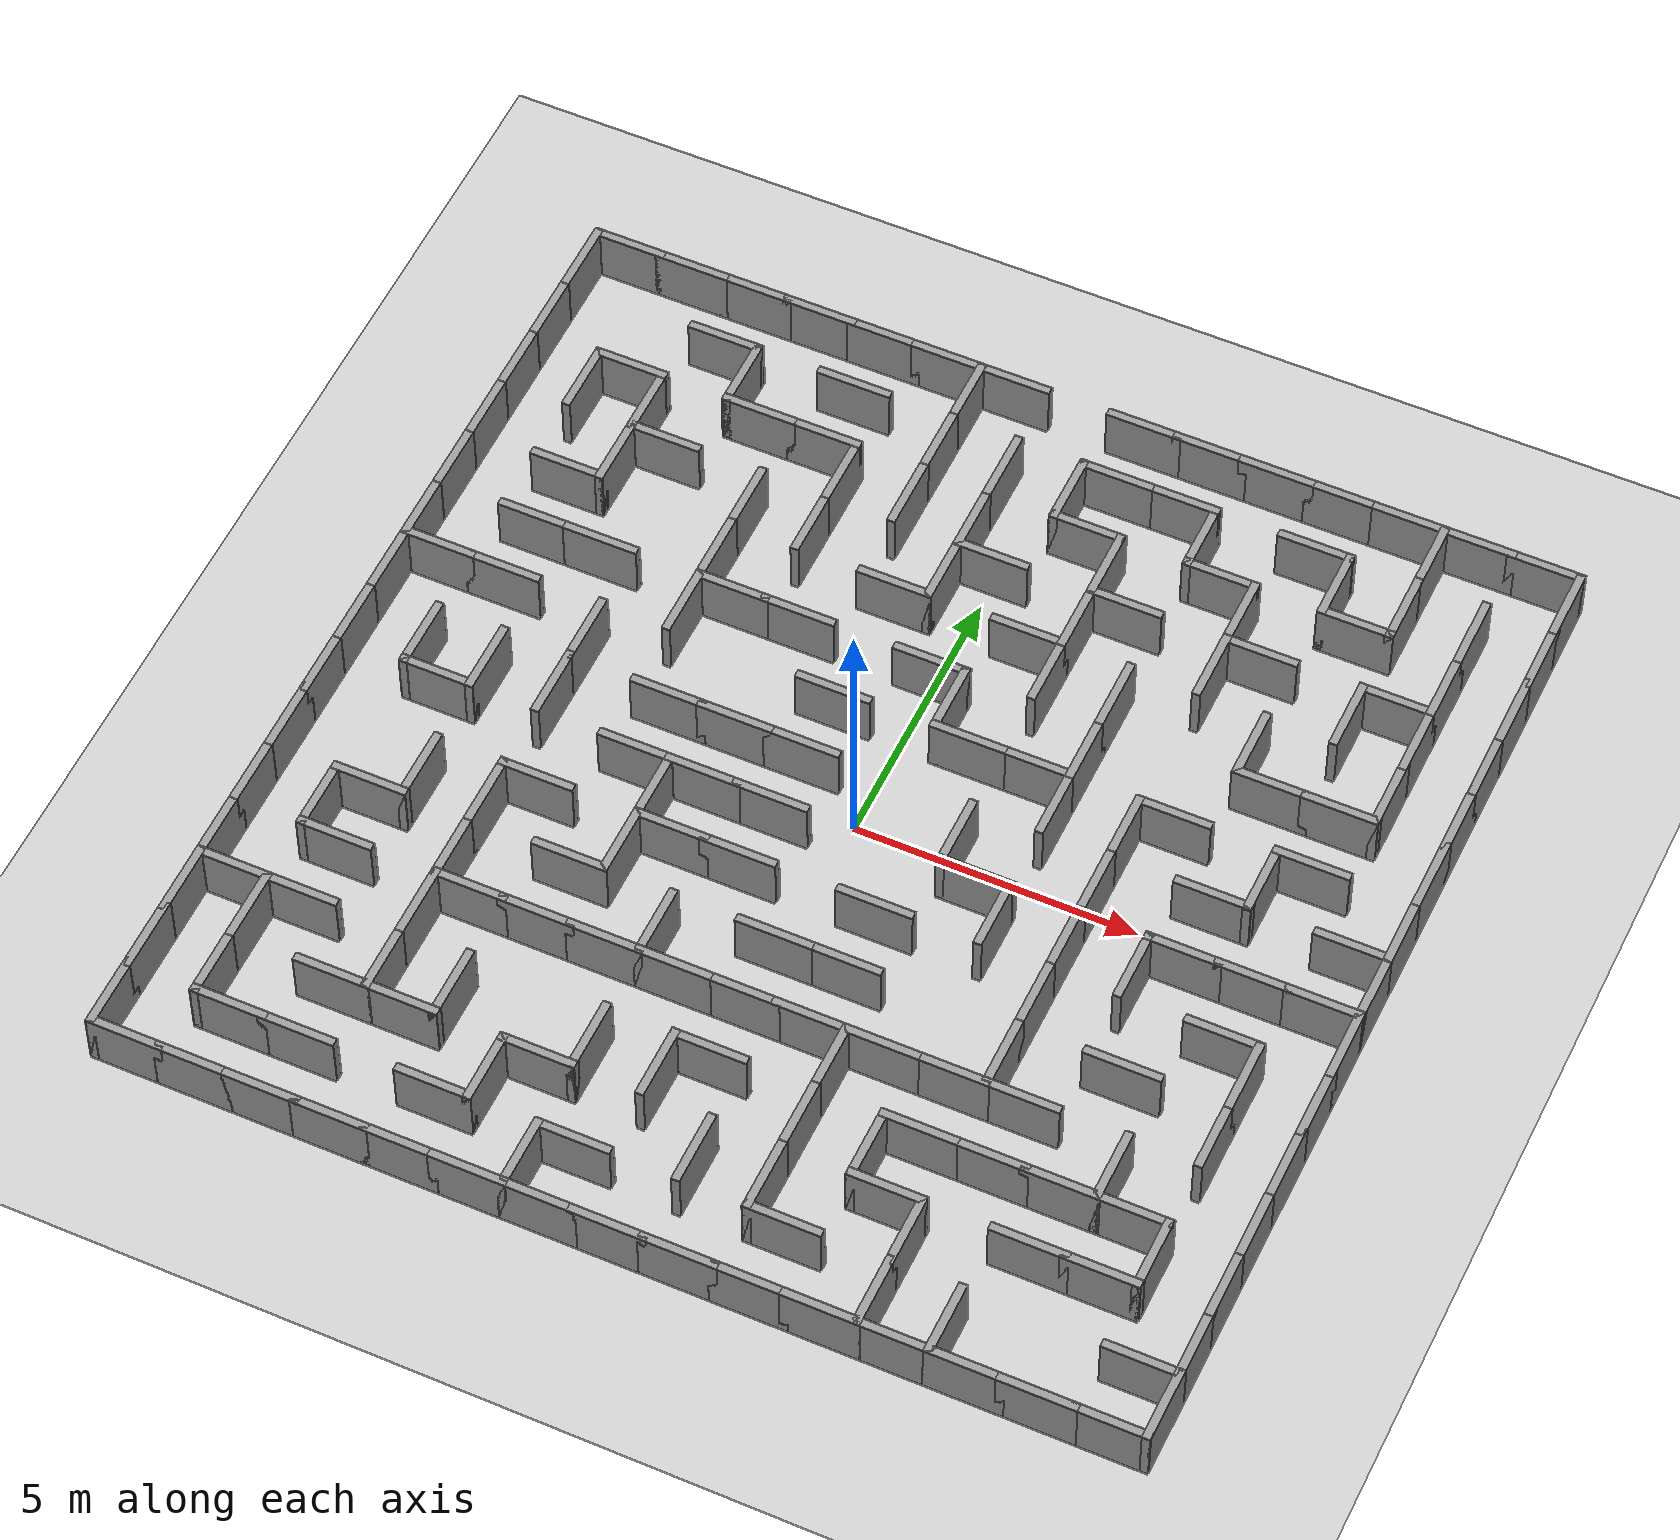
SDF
<?xml version="1.0" ?>
<sdf version="1.6">
  <world name="optimized_maze_world">
    <include><uri>model://sun</uri></include>
    <include><uri>model://ground_plane</uri></include>
    <model name="pledge_maze">
      <static>true</static>
      <link name='maze_link'>

        <collision name='c_0'><pose>-8.4 -9.0 0.5 0 0 0</pose><geometry><box><size>1.3499999999999999 0.15 1.0</size></box></geometry></collision>
        <visual name='v_0'><pose>-8.4 -9.0 0.5 0 0 0</pose><geometry><box><size>1.3499999999999999 0.15 1.0</size></box></geometry><material><ambient>0.6 0.6 0.6 1</ambient></material></visual>
        <collision name='c_1'><pose>-7.2 -9.0 0.5 0 0 0</pose><geometry><box><size>1.3499999999999999 0.15 1.0</size></box></geometry></collision>
        <visual name='v_1'><pose>-7.2 -9.0 0.5 0 0 0</pose><geometry><box><size>1.3499999999999999 0.15 1.0</size></box></geometry><material><ambient>0.6 0.6 0.6 1</ambient></material></visual>
        <collision name='c_2'><pose>-6.0 -9.0 0.5 0 0 0</pose><geometry><box><size>1.3499999999999999 0.15 1.0</size></box></geometry></collision>
        <visual name='v_2'><pose>-6.0 -9.0 0.5 0 0 0</pose><geometry><box><size>1.3499999999999999 0.15 1.0</size></box></geometry><material><ambient>0.6 0.6 0.6 1</ambient></material></visual>
        <collision name='c_3'><pose>-4.800000000000001 -9.0 0.5 0 0 0</pose><geometry><box><size>1.3499999999999999 0.15 1.0</size></box></geometry></collision>
        <visual name='v_3'><pose>-4.800000000000001 -9.0 0.5 0 0 0</pose><geometry><box><size>1.3499999999999999 0.15 1.0</size></box></geometry><material><ambient>0.6 0.6 0.6 1</ambient></material></visual>
        <collision name='c_4'><pose>-3.6000000000000005 -9.0 0.5 0 0 0</pose><geometry><box><size>1.3499999999999999 0.15 1.0</size></box></geometry></collision>
        <visual name='v_4'><pose>-3.6000000000000005 -9.0 0.5 0 0 0</pose><geometry><box><size>1.3499999999999999 0.15 1.0</size></box></geometry><material><ambient>0.6 0.6 0.6 1</ambient></material></visual>
        <collision name='c_5'><pose>-2.4000000000000004 -9.0 0.5 0 0 0</pose><geometry><box><size>1.3499999999999999 0.15 1.0</size></box></geometry></collision>
        <visual name='v_5'><pose>-2.4000000000000004 -9.0 0.5 0 0 0</pose><geometry><box><size>1.3499999999999999 0.15 1.0</size></box></geometry><material><ambient>0.6 0.6 0.6 1</ambient></material></visual>
        <collision name='c_6'><pose>-1.200000000000001 -9.0 0.5 0 0 0</pose><geometry><box><size>1.3499999999999999 0.15 1.0</size></box></geometry></collision>
        <visual name='v_6'><pose>-1.200000000000001 -9.0 0.5 0 0 0</pose><geometry><box><size>1.3499999999999999 0.15 1.0</size></box></geometry><material><ambient>0.6 0.6 0.6 1</ambient></material></visual>
        <collision name='c_7'><pose>0.0 -9.0 0.5 0 0 0</pose><geometry><box><size>1.3499999999999999 0.15 1.0</size></box></geometry></collision>
        <visual name='v_7'><pose>0.0 -9.0 0.5 0 0 0</pose><geometry><box><size>1.3499999999999999 0.15 1.0</size></box></geometry><material><ambient>0.6 0.6 0.6 1</ambient></material></visual>
        <collision name='c_8'><pose>1.1999999999999993 -9.0 0.5 0 0 0</pose><geometry><box><size>1.3499999999999999 0.15 1.0</size></box></geometry></collision>
        <visual name='v_8'><pose>1.1999999999999993 -9.0 0.5 0 0 0</pose><geometry><box><size>1.3499999999999999 0.15 1.0</size></box></geometry><material><ambient>0.6 0.6 0.6 1</ambient></material></visual>
        <collision name='c_9'><pose>2.3999999999999986 -9.0 0.5 0 0 0</pose><geometry><box><size>1.3499999999999999 0.15 1.0</size></box></geometry></collision>
        <visual name='v_9'><pose>2.3999999999999986 -9.0 0.5 0 0 0</pose><geometry><box><size>1.3499999999999999 0.15 1.0</size></box></geometry><material><ambient>0.6 0.6 0.6 1</ambient></material></visual>
        <collision name='c_10'><pose>3.5999999999999996 -9.0 0.5 0 0 0</pose><geometry><box><size>1.3499999999999999 0.15 1.0</size></box></geometry></collision>
        <visual name='v_10'><pose>3.5999999999999996 -9.0 0.5 0 0 0</pose><geometry><box><size>1.3499999999999999 0.15 1.0</size></box></geometry><material><ambient>0.6 0.6 0.6 1</ambient></material></visual>
        <collision name='c_11'><pose>4.799999999999999 -9.0 0.5 0 0 0</pose><geometry><box><size>1.3499999999999999 0.15 1.0</size></box></geometry></collision>
        <visual name='v_11'><pose>4.799999999999999 -9.0 0.5 0 0 0</pose><geometry><box><size>1.3499999999999999 0.15 1.0</size></box></geometry><material><ambient>0.6 0.6 0.6 1</ambient></material></visual>
        <collision name='c_12'><pose>5.999999999999998 -9.0 0.5 0 0 0</pose><geometry><box><size>1.3499999999999999 0.15 1.0</size></box></geometry></collision>
        <visual name='v_12'><pose>5.999999999999998 -9.0 0.5 0 0 0</pose><geometry><box><size>1.3499999999999999 0.15 1.0</size></box></geometry><material><ambient>0.6 0.6 0.6 1</ambient></material></visual>
        <collision name='c_13'><pose>7.199999999999999 -9.0 0.5 0 0 0</pose><geometry><box><size>1.3499999999999999 0.15 1.0</size></box></geometry></collision>
        <visual name='v_13'><pose>7.199999999999999 -9.0 0.5 0 0 0</pose><geometry><box><size>1.3499999999999999 0.15 1.0</size></box></geometry><material><ambient>0.6 0.6 0.6 1</ambient></material></visual>
        <collision name='c_14'><pose>8.400000000000002 -9.0 0.5 0 0 0</pose><geometry><box><size>1.3499999999999999 0.15 1.0</size></box></geometry></collision>
        <visual name='v_14'><pose>8.400000000000002 -9.0 0.5 0 0 0</pose><geometry><box><size>1.3499999999999999 0.15 1.0</size></box></geometry><material><ambient>0.6 0.6 0.6 1</ambient></material></visual>
        <collision name='c_15'><pose>-7.2 -7.8 0.5 0 0 0</pose><geometry><box><size>1.3499999999999999 0.15 1.0</size></box></geometry></collision>
        <visual name='v_15'><pose>-7.2 -7.8 0.5 0 0 0</pose><geometry><box><size>1.3499999999999999 0.15 1.0</size></box></geometry><material><ambient>0.6 0.6 0.6 1</ambient></material></visual>
        <collision name='c_16'><pose>-6.0 -7.8 0.5 0 0 0</pose><geometry><box><size>1.3499999999999999 0.15 1.0</size></box></geometry></collision>
        <visual name='v_16'><pose>-6.0 -7.8 0.5 0 0 0</pose><geometry><box><size>1.3499999999999999 0.15 1.0</size></box></geometry><material><ambient>0.6 0.6 0.6 1</ambient></material></visual>
        <collision name='c_17'><pose>-3.6000000000000005 -7.8 0.5 0 0 0</pose><geometry><box><size>1.3499999999999999 0.15 1.0</size></box></geometry></collision>
        <visual name='v_17'><pose>-3.6000000000000005 -7.8 0.5 0 0 0</pose><geometry><box><size>1.3499999999999999 0.15 1.0</size></box></geometry><material><ambient>0.6 0.6 0.6 1</ambient></material></visual>
        <collision name='c_18'><pose>-1.200000000000001 -7.8 0.5 0 0 0</pose><geometry><box><size>1.3499999999999999 0.15 1.0</size></box></geometry></collision>
        <visual name='v_18'><pose>-1.200000000000001 -7.8 0.5 0 0 0</pose><geometry><box><size>1.3499999999999999 0.15 1.0</size></box></geometry><material><ambient>0.6 0.6 0.6 1</ambient></material></visual>
        <collision name='c_19'><pose>2.3999999999999986 -7.8 0.5 0 0 0</pose><geometry><box><size>1.3499999999999999 0.15 1.0</size></box></geometry></collision>
        <visual name='v_19'><pose>2.3999999999999986 -7.8 0.5 0 0 0</pose><geometry><box><size>1.3499999999999999 0.15 1.0</size></box></geometry><material><ambient>0.6 0.6 0.6 1</ambient></material></visual>
        <collision name='c_20'><pose>8.400000000000002 -7.8 0.5 0 0 0</pose><geometry><box><size>1.3499999999999999 0.15 1.0</size></box></geometry></collision>
        <visual name='v_20'><pose>8.400000000000002 -7.8 0.5 0 0 0</pose><geometry><box><size>1.3499999999999999 0.15 1.0</size></box></geometry><material><ambient>0.6 0.6 0.6 1</ambient></material></visual>
        <collision name='c_21'><pose>-6.0 -6.6 0.5 0 0 0</pose><geometry><box><size>1.3499999999999999 0.15 1.0</size></box></geometry></collision>
        <visual name='v_21'><pose>-6.0 -6.6 0.5 0 0 0</pose><geometry><box><size>1.3499999999999999 0.15 1.0</size></box></geometry><material><ambient>0.6 0.6 0.6 1</ambient></material></visual>
        <collision name='c_22'><pose>-4.800000000000001 -6.6 0.5 0 0 0</pose><geometry><box><size>1.3499999999999999 0.15 1.0</size></box></geometry></collision>
        <visual name='v_22'><pose>-4.800000000000001 -6.6 0.5 0 0 0</pose><geometry><box><size>1.3499999999999999 0.15 1.0</size></box></geometry><material><ambient>0.6 0.6 0.6 1</ambient></material></visual>
        <collision name='c_23'><pose>-2.4000000000000004 -6.6 0.5 0 0 0</pose><geometry><box><size>1.3499999999999999 0.15 1.0</size></box></geometry></collision>
        <visual name='v_23'><pose>-2.4000000000000004 -6.6 0.5 0 0 0</pose><geometry><box><size>1.3499999999999999 0.15 1.0</size></box></geometry><material><ambient>0.6 0.6 0.6 1</ambient></material></visual>
        <collision name='c_24'><pose>3.5999999999999996 -6.6 0.5 0 0 0</pose><geometry><box><size>1.3499999999999999 0.15 1.0</size></box></geometry></collision>
        <visual name='v_24'><pose>3.5999999999999996 -6.6 0.5 0 0 0</pose><geometry><box><size>1.3499999999999999 0.15 1.0</size></box></geometry><material><ambient>0.6 0.6 0.6 1</ambient></material></visual>
        <collision name='c_25'><pose>5.999999999999998 -6.6 0.5 0 0 0</pose><geometry><box><size>1.3499999999999999 0.15 1.0</size></box></geometry></collision>
        <visual name='v_25'><pose>5.999999999999998 -6.6 0.5 0 0 0</pose><geometry><box><size>1.3499999999999999 0.15 1.0</size></box></geometry><material><ambient>0.6 0.6 0.6 1</ambient></material></visual>
        <collision name='c_26'><pose>7.199999999999999 -6.6 0.5 0 0 0</pose><geometry><box><size>1.3499999999999999 0.15 1.0</size></box></geometry></collision>
        <visual name='v_26'><pose>7.199999999999999 -6.6 0.5 0 0 0</pose><geometry><box><size>1.3499999999999999 0.15 1.0</size></box></geometry><material><ambient>0.6 0.6 0.6 1</ambient></material></visual>
        <collision name='c_27'><pose>-8.4 -5.4 0.5 0 0 0</pose><geometry><box><size>1.3499999999999999 0.15 1.0</size></box></geometry></collision>
        <visual name='v_27'><pose>-8.4 -5.4 0.5 0 0 0</pose><geometry><box><size>1.3499999999999999 0.15 1.0</size></box></geometry><material><ambient>0.6 0.6 0.6 1</ambient></material></visual>
        <collision name='c_28'><pose>-7.2 -5.4 0.5 0 0 0</pose><geometry><box><size>1.3499999999999999 0.15 1.0</size></box></geometry></collision>
        <visual name='v_28'><pose>-7.2 -5.4 0.5 0 0 0</pose><geometry><box><size>1.3499999999999999 0.15 1.0</size></box></geometry><material><ambient>0.6 0.6 0.6 1</ambient></material></visual>
        <collision name='c_29'><pose>0.0 -5.4 0.5 0 0 0</pose><geometry><box><size>1.3499999999999999 0.15 1.0</size></box></geometry></collision>
        <visual name='v_29'><pose>0.0 -5.4 0.5 0 0 0</pose><geometry><box><size>1.3499999999999999 0.15 1.0</size></box></geometry><material><ambient>0.6 0.6 0.6 1</ambient></material></visual>
        <collision name='c_30'><pose>3.5999999999999996 -5.4 0.5 0 0 0</pose><geometry><box><size>1.3499999999999999 0.15 1.0</size></box></geometry></collision>
        <visual name='v_30'><pose>3.5999999999999996 -5.4 0.5 0 0 0</pose><geometry><box><size>1.3499999999999999 0.15 1.0</size></box></geometry><material><ambient>0.6 0.6 0.6 1</ambient></material></visual>
        <collision name='c_31'><pose>4.799999999999999 -5.4 0.5 0 0 0</pose><geometry><box><size>1.3499999999999999 0.15 1.0</size></box></geometry></collision>
        <visual name='v_31'><pose>4.799999999999999 -5.4 0.5 0 0 0</pose><geometry><box><size>1.3499999999999999 0.15 1.0</size></box></geometry><material><ambient>0.6 0.6 0.6 1</ambient></material></visual>
        <collision name='c_32'><pose>5.999999999999998 -5.4 0.5 0 0 0</pose><geometry><box><size>1.3499999999999999 0.15 1.0</size></box></geometry></collision>
        <visual name='v_32'><pose>5.999999999999998 -5.4 0.5 0 0 0</pose><geometry><box><size>1.3499999999999999 0.15 1.0</size></box></geometry><material><ambient>0.6 0.6 0.6 1</ambient></material></visual>
        <collision name='c_33'><pose>7.199999999999999 -5.4 0.5 0 0 0</pose><geometry><box><size>1.3499999999999999 0.15 1.0</size></box></geometry></collision>
        <visual name='v_33'><pose>7.199999999999999 -5.4 0.5 0 0 0</pose><geometry><box><size>1.3499999999999999 0.15 1.0</size></box></geometry><material><ambient>0.6 0.6 0.6 1</ambient></material></visual>
        <collision name='c_34'><pose>-7.2 -4.2 0.5 0 0 0</pose><geometry><box><size>1.3499999999999999 0.15 1.0</size></box></geometry></collision>
        <visual name='v_34'><pose>-7.2 -4.2 0.5 0 0 0</pose><geometry><box><size>1.3499999999999999 0.15 1.0</size></box></geometry><material><ambient>0.6 0.6 0.6 1</ambient></material></visual>
        <collision name='c_35'><pose>-4.800000000000001 -4.2 0.5 0 0 0</pose><geometry><box><size>1.3499999999999999 0.15 1.0</size></box></geometry></collision>
        <visual name='v_35'><pose>-4.800000000000001 -4.2 0.5 0 0 0</pose><geometry><box><size>1.3499999999999999 0.15 1.0</size></box></geometry><material><ambient>0.6 0.6 0.6 1</ambient></material></visual>
        <collision name='c_36'><pose>-3.6000000000000005 -4.2 0.5 0 0 0</pose><geometry><box><size>1.3499999999999999 0.15 1.0</size></box></geometry></collision>
        <visual name='v_36'><pose>-3.6000000000000005 -4.2 0.5 0 0 0</pose><geometry><box><size>1.3499999999999999 0.15 1.0</size></box></geometry><material><ambient>0.6 0.6 0.6 1</ambient></material></visual>
        <collision name='c_37'><pose>-2.4000000000000004 -4.2 0.5 0 0 0</pose><geometry><box><size>1.3499999999999999 0.15 1.0</size></box></geometry></collision>
        <visual name='v_37'><pose>-2.4000000000000004 -4.2 0.5 0 0 0</pose><geometry><box><size>1.3499999999999999 0.15 1.0</size></box></geometry><material><ambient>0.6 0.6 0.6 1</ambient></material></visual>
        <collision name='c_38'><pose>-1.200000000000001 -4.2 0.5 0 0 0</pose><geometry><box><size>1.3499999999999999 0.15 1.0</size></box></geometry></collision>
        <visual name='v_38'><pose>-1.200000000000001 -4.2 0.5 0 0 0</pose><geometry><box><size>1.3499999999999999 0.15 1.0</size></box></geometry><material><ambient>0.6 0.6 0.6 1</ambient></material></visual>
        <collision name='c_39'><pose>0.0 -4.2 0.5 0 0 0</pose><geometry><box><size>1.3499999999999999 0.15 1.0</size></box></geometry></collision>
        <visual name='v_39'><pose>0.0 -4.2 0.5 0 0 0</pose><geometry><box><size>1.3499999999999999 0.15 1.0</size></box></geometry><material><ambient>0.6 0.6 0.6 1</ambient></material></visual>
        <collision name='c_40'><pose>1.1999999999999993 -4.2 0.5 0 0 0</pose><geometry><box><size>1.3499999999999999 0.15 1.0</size></box></geometry></collision>
        <visual name='v_40'><pose>1.1999999999999993 -4.2 0.5 0 0 0</pose><geometry><box><size>1.3499999999999999 0.15 1.0</size></box></geometry><material><ambient>0.6 0.6 0.6 1</ambient></material></visual>
        <collision name='c_41'><pose>2.3999999999999986 -4.2 0.5 0 0 0</pose><geometry><box><size>1.3499999999999999 0.15 1.0</size></box></geometry></collision>
        <visual name='v_41'><pose>2.3999999999999986 -4.2 0.5 0 0 0</pose><geometry><box><size>1.3499999999999999 0.15 1.0</size></box></geometry><material><ambient>0.6 0.6 0.6 1</ambient></material></visual>
        <collision name='c_42'><pose>3.5999999999999996 -4.2 0.5 0 0 0</pose><geometry><box><size>1.3499999999999999 0.15 1.0</size></box></geometry></collision>
        <visual name='v_42'><pose>3.5999999999999996 -4.2 0.5 0 0 0</pose><geometry><box><size>1.3499999999999999 0.15 1.0</size></box></geometry><material><ambient>0.6 0.6 0.6 1</ambient></material></visual>
        <collision name='c_43'><pose>4.799999999999999 -4.2 0.5 0 0 0</pose><geometry><box><size>1.3499999999999999 0.15 1.0</size></box></geometry></collision>
        <visual name='v_43'><pose>4.799999999999999 -4.2 0.5 0 0 0</pose><geometry><box><size>1.3499999999999999 0.15 1.0</size></box></geometry><material><ambient>0.6 0.6 0.6 1</ambient></material></visual>
        <collision name='c_44'><pose>-7.2 -3.0 0.5 0 0 0</pose><geometry><box><size>1.3499999999999999 0.15 1.0</size></box></geometry></collision>
        <visual name='v_44'><pose>-7.2 -3.0 0.5 0 0 0</pose><geometry><box><size>1.3499999999999999 0.15 1.0</size></box></geometry><material><ambient>0.6 0.6 0.6 1</ambient></material></visual>
        <collision name='c_45'><pose>-3.6000000000000005 -3.0 0.5 0 0 0</pose><geometry><box><size>1.3499999999999999 0.15 1.0</size></box></geometry></collision>
        <visual name='v_45'><pose>-3.6000000000000005 -3.0 0.5 0 0 0</pose><geometry><box><size>1.3499999999999999 0.15 1.0</size></box></geometry><material><ambient>0.6 0.6 0.6 1</ambient></material></visual>
        <collision name='c_46'><pose>0.0 -3.0 0.5 0 0 0</pose><geometry><box><size>1.3499999999999999 0.15 1.0</size></box></geometry></collision>
        <visual name='v_46'><pose>0.0 -3.0 0.5 0 0 0</pose><geometry><box><size>1.3499999999999999 0.15 1.0</size></box></geometry><material><ambient>0.6 0.6 0.6 1</ambient></material></visual>
        <collision name='c_47'><pose>1.1999999999999993 -3.0 0.5 0 0 0</pose><geometry><box><size>1.3499999999999999 0.15 1.0</size></box></geometry></collision>
        <visual name='v_47'><pose>1.1999999999999993 -3.0 0.5 0 0 0</pose><geometry><box><size>1.3499999999999999 0.15 1.0</size></box></geometry><material><ambient>0.6 0.6 0.6 1</ambient></material></visual>
        <collision name='c_48'><pose>5.999999999999998 -3.0 0.5 0 0 0</pose><geometry><box><size>1.3499999999999999 0.15 1.0</size></box></geometry></collision>
        <visual name='v_48'><pose>5.999999999999998 -3.0 0.5 0 0 0</pose><geometry><box><size>1.3499999999999999 0.15 1.0</size></box></geometry><material><ambient>0.6 0.6 0.6 1</ambient></material></visual>
        <collision name='c_49'><pose>-4.800000000000001 -1.8000000000000007 0.5 0 0 0</pose><geometry><box><size>1.3499999999999999 0.15 1.0</size></box></geometry></collision>
        <visual name='v_49'><pose>-4.800000000000001 -1.8000000000000007 0.5 0 0 0</pose><geometry><box><size>1.3499999999999999 0.15 1.0</size></box></geometry><material><ambient>0.6 0.6 0.6 1</ambient></material></visual>
        <collision name='c_50'><pose>-2.4000000000000004 -1.8000000000000007 0.5 0 0 0</pose><geometry><box><size>1.3499999999999999 0.15 1.0</size></box></geometry></collision>
        <visual name='v_50'><pose>-2.4000000000000004 -1.8000000000000007 0.5 0 0 0</pose><geometry><box><size>1.3499999999999999 0.15 1.0</size></box></geometry><material><ambient>0.6 0.6 0.6 1</ambient></material></visual>
        <collision name='c_51'><pose>-1.200000000000001 -1.8000000000000007 0.5 0 0 0</pose><geometry><box><size>1.3499999999999999 0.15 1.0</size></box></geometry></collision>
        <visual name='v_51'><pose>-1.200000000000001 -1.8000000000000007 0.5 0 0 0</pose><geometry><box><size>1.3499999999999999 0.15 1.0</size></box></geometry><material><ambient>0.6 0.6 0.6 1</ambient></material></visual>
        <collision name='c_52'><pose>1.1999999999999993 -1.8000000000000007 0.5 0 0 0</pose><geometry><box><size>1.3499999999999999 0.15 1.0</size></box></geometry></collision>
        <visual name='v_52'><pose>1.1999999999999993 -1.8000000000000007 0.5 0 0 0</pose><geometry><box><size>1.3499999999999999 0.15 1.0</size></box></geometry><material><ambient>0.6 0.6 0.6 1</ambient></material></visual>
        <collision name='c_53'><pose>7.199999999999999 -1.8000000000000007 0.5 0 0 0</pose><geometry><box><size>1.3499999999999999 0.15 1.0</size></box></geometry></collision>
        <visual name='v_53'><pose>7.199999999999999 -1.8000000000000007 0.5 0 0 0</pose><geometry><box><size>1.3499999999999999 0.15 1.0</size></box></geometry><material><ambient>0.6 0.6 0.6 1</ambient></material></visual>
        <collision name='c_54'><pose>-7.2 -0.5999999999999996 0.5 0 0 0</pose><geometry><box><size>1.3499999999999999 0.15 1.0</size></box></geometry></collision>
        <visual name='v_54'><pose>-7.2 -0.5999999999999996 0.5 0 0 0</pose><geometry><box><size>1.3499999999999999 0.15 1.0</size></box></geometry><material><ambient>0.6 0.6 0.6 1</ambient></material></visual>
        <collision name='c_55'><pose>-3.6000000000000005 -0.5999999999999996 0.5 0 0 0</pose><geometry><box><size>1.3499999999999999 0.15 1.0</size></box></geometry></collision>
        <visual name='v_55'><pose>-3.6000000000000005 -0.5999999999999996 0.5 0 0 0</pose><geometry><box><size>1.3499999999999999 0.15 1.0</size></box></geometry><material><ambient>0.6 0.6 0.6 1</ambient></material></visual>
        <collision name='c_56'><pose>-2.4000000000000004 -0.5999999999999996 0.5 0 0 0</pose><geometry><box><size>1.3499999999999999 0.15 1.0</size></box></geometry></collision>
        <visual name='v_56'><pose>-2.4000000000000004 -0.5999999999999996 0.5 0 0 0</pose><geometry><box><size>1.3499999999999999 0.15 1.0</size></box></geometry><material><ambient>0.6 0.6 0.6 1</ambient></material></visual>
        <collision name='c_57'><pose>-1.200000000000001 -0.5999999999999996 0.5 0 0 0</pose><geometry><box><size>1.3499999999999999 0.15 1.0</size></box></geometry></collision>
        <visual name='v_57'><pose>-1.200000000000001 -0.5999999999999996 0.5 0 0 0</pose><geometry><box><size>1.3499999999999999 0.15 1.0</size></box></geometry><material><ambient>0.6 0.6 0.6 1</ambient></material></visual>
        <collision name='c_58'><pose>2.3999999999999986 -0.5999999999999996 0.5 0 0 0</pose><geometry><box><size>1.3499999999999999 0.15 1.0</size></box></geometry></collision>
        <visual name='v_58'><pose>2.3999999999999986 -0.5999999999999996 0.5 0 0 0</pose><geometry><box><size>1.3499999999999999 0.15 1.0</size></box></geometry><material><ambient>0.6 0.6 0.6 1</ambient></material></visual>
        <collision name='c_59'><pose>5.999999999999998 -0.5999999999999996 0.5 0 0 0</pose><geometry><box><size>1.3499999999999999 0.15 1.0</size></box></geometry></collision>
        <visual name='v_59'><pose>5.999999999999998 -0.5999999999999996 0.5 0 0 0</pose><geometry><box><size>1.3499999999999999 0.15 1.0</size></box></geometry><material><ambient>0.6 0.6 0.6 1</ambient></material></visual>
        <collision name='c_60'><pose>7.199999999999999 -0.5999999999999996 0.5 0 0 0</pose><geometry><box><size>1.3499999999999999 0.15 1.0</size></box></geometry></collision>
        <visual name='v_60'><pose>7.199999999999999 -0.5999999999999996 0.5 0 0 0</pose><geometry><box><size>1.3499999999999999 0.15 1.0</size></box></geometry><material><ambient>0.6 0.6 0.6 1</ambient></material></visual>
        <collision name='c_61'><pose>8.400000000000002 -0.5999999999999996 0.5 0 0 0</pose><geometry><box><size>1.3499999999999999 0.15 1.0</size></box></geometry></collision>
        <visual name='v_61'><pose>8.400000000000002 -0.5999999999999996 0.5 0 0 0</pose><geometry><box><size>1.3499999999999999 0.15 1.0</size></box></geometry><material><ambient>0.6 0.6 0.6 1</ambient></material></visual>
        <collision name='c_62'><pose>-3.6000000000000005 0.5999999999999996 0.5 0 0 0</pose><geometry><box><size>1.3499999999999999 0.15 1.0</size></box></geometry></collision>
        <visual name='v_62'><pose>-3.6000000000000005 0.5999999999999996 0.5 0 0 0</pose><geometry><box><size>1.3499999999999999 0.15 1.0</size></box></geometry><material><ambient>0.6 0.6 0.6 1</ambient></material></visual>
        <collision name='c_63'><pose>-2.4000000000000004 0.5999999999999996 0.5 0 0 0</pose><geometry><box><size>1.3499999999999999 0.15 1.0</size></box></geometry></collision>
        <visual name='v_63'><pose>-2.4000000000000004 0.5999999999999996 0.5 0 0 0</pose><geometry><box><size>1.3499999999999999 0.15 1.0</size></box></geometry><material><ambient>0.6 0.6 0.6 1</ambient></material></visual>
        <collision name='c_64'><pose>-1.200000000000001 0.5999999999999996 0.5 0 0 0</pose><geometry><box><size>1.3499999999999999 0.15 1.0</size></box></geometry></collision>
        <visual name='v_64'><pose>-1.200000000000001 0.5999999999999996 0.5 0 0 0</pose><geometry><box><size>1.3499999999999999 0.15 1.0</size></box></geometry><material><ambient>0.6 0.6 0.6 1</ambient></material></visual>
        <collision name='c_65'><pose>5.999999999999998 0.5999999999999996 0.5 0 0 0</pose><geometry><box><size>1.3499999999999999 0.15 1.0</size></box></geometry></collision>
        <visual name='v_65'><pose>5.999999999999998 0.5999999999999996 0.5 0 0 0</pose><geometry><box><size>1.3499999999999999 0.15 1.0</size></box></geometry><material><ambient>0.6 0.6 0.6 1</ambient></material></visual>
        <collision name='c_66'><pose>8.400000000000002 0.5999999999999996 0.5 0 0 0</pose><geometry><box><size>1.3499999999999999 0.15 1.0</size></box></geometry></collision>
        <visual name='v_66'><pose>8.400000000000002 0.5999999999999996 0.5 0 0 0</pose><geometry><box><size>1.3499999999999999 0.15 1.0</size></box></geometry><material><ambient>0.6 0.6 0.6 1</ambient></material></visual>
        <collision name='c_67'><pose>-8.4 1.799999999999999 0.5 0 0 0</pose><geometry><box><size>1.3499999999999999 0.15 1.0</size></box></geometry></collision>
        <visual name='v_67'><pose>-8.4 1.799999999999999 0.5 0 0 0</pose><geometry><box><size>1.3499999999999999 0.15 1.0</size></box></geometry><material><ambient>0.6 0.6 0.6 1</ambient></material></visual>
        <collision name='c_68'><pose>-7.2 1.799999999999999 0.5 0 0 0</pose><geometry><box><size>1.3499999999999999 0.15 1.0</size></box></geometry></collision>
        <visual name='v_68'><pose>-7.2 1.799999999999999 0.5 0 0 0</pose><geometry><box><size>1.3499999999999999 0.15 1.0</size></box></geometry><material><ambient>0.6 0.6 0.6 1</ambient></material></visual>
        <collision name='c_69'><pose>-1.200000000000001 1.799999999999999 0.5 0 0 0</pose><geometry><box><size>1.3499999999999999 0.15 1.0</size></box></geometry></collision>
        <visual name='v_69'><pose>-1.200000000000001 1.799999999999999 0.5 0 0 0</pose><geometry><box><size>1.3499999999999999 0.15 1.0</size></box></geometry><material><ambient>0.6 0.6 0.6 1</ambient></material></visual>
        <collision name='c_70'><pose>1.1999999999999993 1.799999999999999 0.5 0 0 0</pose><geometry><box><size>1.3499999999999999 0.15 1.0</size></box></geometry></collision>
        <visual name='v_70'><pose>1.1999999999999993 1.799999999999999 0.5 0 0 0</pose><geometry><box><size>1.3499999999999999 0.15 1.0</size></box></geometry><material><ambient>0.6 0.6 0.6 1</ambient></material></visual>
        <collision name='c_71'><pose>2.3999999999999986 1.799999999999999 0.5 0 0 0</pose><geometry><box><size>1.3499999999999999 0.15 1.0</size></box></geometry></collision>
        <visual name='v_71'><pose>2.3999999999999986 1.799999999999999 0.5 0 0 0</pose><geometry><box><size>1.3499999999999999 0.15 1.0</size></box></geometry><material><ambient>0.6 0.6 0.6 1</ambient></material></visual>
        <collision name='c_72'><pose>4.799999999999999 1.799999999999999 0.5 0 0 0</pose><geometry><box><size>1.3499999999999999 0.15 1.0</size></box></geometry></collision>
        <visual name='v_72'><pose>4.799999999999999 1.799999999999999 0.5 0 0 0</pose><geometry><box><size>1.3499999999999999 0.15 1.0</size></box></geometry><material><ambient>0.6 0.6 0.6 1</ambient></material></visual>
        <collision name='c_73'><pose>7.199999999999999 1.799999999999999 0.5 0 0 0</pose><geometry><box><size>1.3499999999999999 0.15 1.0</size></box></geometry></collision>
        <visual name='v_73'><pose>7.199999999999999 1.799999999999999 0.5 0 0 0</pose><geometry><box><size>1.3499999999999999 0.15 1.0</size></box></geometry><material><ambient>0.6 0.6 0.6 1</ambient></material></visual>
        <collision name='c_74'><pose>-7.2 3.0 0.5 0 0 0</pose><geometry><box><size>1.3499999999999999 0.15 1.0</size></box></geometry></collision>
        <visual name='v_74'><pose>-7.2 3.0 0.5 0 0 0</pose><geometry><box><size>1.3499999999999999 0.15 1.0</size></box></geometry><material><ambient>0.6 0.6 0.6 1</ambient></material></visual>
        <collision name='c_75'><pose>-6.0 3.0 0.5 0 0 0</pose><geometry><box><size>1.3499999999999999 0.15 1.0</size></box></geometry></collision>
        <visual name='v_75'><pose>-6.0 3.0 0.5 0 0 0</pose><geometry><box><size>1.3499999999999999 0.15 1.0</size></box></geometry><material><ambient>0.6 0.6 0.6 1</ambient></material></visual>
        <collision name='c_76'><pose>-3.6000000000000005 3.0 0.5 0 0 0</pose><geometry><box><size>1.3499999999999999 0.15 1.0</size></box></geometry></collision>
        <visual name='v_76'><pose>-3.6000000000000005 3.0 0.5 0 0 0</pose><geometry><box><size>1.3499999999999999 0.15 1.0</size></box></geometry><material><ambient>0.6 0.6 0.6 1</ambient></material></visual>
        <collision name='c_77'><pose>-2.4000000000000004 3.0 0.5 0 0 0</pose><geometry><box><size>1.3499999999999999 0.15 1.0</size></box></geometry></collision>
        <visual name='v_77'><pose>-2.4000000000000004 3.0 0.5 0 0 0</pose><geometry><box><size>1.3499999999999999 0.15 1.0</size></box></geometry><material><ambient>0.6 0.6 0.6 1</ambient></material></visual>
        <collision name='c_78'><pose>0.0 3.0 0.5 0 0 0</pose><geometry><box><size>1.3499999999999999 0.15 1.0</size></box></geometry></collision>
        <visual name='v_78'><pose>0.0 3.0 0.5 0 0 0</pose><geometry><box><size>1.3499999999999999 0.15 1.0</size></box></geometry><material><ambient>0.6 0.6 0.6 1</ambient></material></visual>
        <collision name='c_79'><pose>5.999999999999998 3.0 0.5 0 0 0</pose><geometry><box><size>1.3499999999999999 0.15 1.0</size></box></geometry></collision>
        <visual name='v_79'><pose>5.999999999999998 3.0 0.5 0 0 0</pose><geometry><box><size>1.3499999999999999 0.15 1.0</size></box></geometry><material><ambient>0.6 0.6 0.6 1</ambient></material></visual>
        <collision name='c_80'><pose>7.199999999999999 3.0 0.5 0 0 0</pose><geometry><box><size>1.3499999999999999 0.15 1.0</size></box></geometry></collision>
        <visual name='v_80'><pose>7.199999999999999 3.0 0.5 0 0 0</pose><geometry><box><size>1.3499999999999999 0.15 1.0</size></box></geometry><material><ambient>0.6 0.6 0.6 1</ambient></material></visual>
        <collision name='c_81'><pose>-7.2 4.199999999999999 0.5 0 0 0</pose><geometry><box><size>1.3499999999999999 0.15 1.0</size></box></geometry></collision>
        <visual name='v_81'><pose>-7.2 4.199999999999999 0.5 0 0 0</pose><geometry><box><size>1.3499999999999999 0.15 1.0</size></box></geometry><material><ambient>0.6 0.6 0.6 1</ambient></material></visual>
        <collision name='c_82'><pose>-1.200000000000001 4.199999999999999 0.5 0 0 0</pose><geometry><box><size>1.3499999999999999 0.15 1.0</size></box></geometry></collision>
        <visual name='v_82'><pose>-1.200000000000001 4.199999999999999 0.5 0 0 0</pose><geometry><box><size>1.3499999999999999 0.15 1.0</size></box></geometry><material><ambient>0.6 0.6 0.6 1</ambient></material></visual>
        <collision name='c_83'><pose>1.1999999999999993 4.199999999999999 0.5 0 0 0</pose><geometry><box><size>1.3499999999999999 0.15 1.0</size></box></geometry></collision>
        <visual name='v_83'><pose>1.1999999999999993 4.199999999999999 0.5 0 0 0</pose><geometry><box><size>1.3499999999999999 0.15 1.0</size></box></geometry><material><ambient>0.6 0.6 0.6 1</ambient></material></visual>
        <collision name='c_84'><pose>-6.0 5.399999999999999 0.5 0 0 0</pose><geometry><box><size>1.3499999999999999 0.15 1.0</size></box></geometry></collision>
        <visual name='v_84'><pose>-6.0 5.399999999999999 0.5 0 0 0</pose><geometry><box><size>1.3499999999999999 0.15 1.0</size></box></geometry><material><ambient>0.6 0.6 0.6 1</ambient></material></visual>
        <collision name='c_85'><pose>0.0 5.399999999999999 0.5 0 0 0</pose><geometry><box><size>1.3499999999999999 0.15 1.0</size></box></geometry></collision>
        <visual name='v_85'><pose>0.0 5.399999999999999 0.5 0 0 0</pose><geometry><box><size>1.3499999999999999 0.15 1.0</size></box></geometry><material><ambient>0.6 0.6 0.6 1</ambient></material></visual>
        <collision name='c_86'><pose>2.3999999999999986 5.399999999999999 0.5 0 0 0</pose><geometry><box><size>1.3499999999999999 0.15 1.0</size></box></geometry></collision>
        <visual name='v_86'><pose>2.3999999999999986 5.399999999999999 0.5 0 0 0</pose><geometry><box><size>1.3499999999999999 0.15 1.0</size></box></geometry><material><ambient>0.6 0.6 0.6 1</ambient></material></visual>
        <collision name='c_87'><pose>4.799999999999999 5.399999999999999 0.5 0 0 0</pose><geometry><box><size>1.3499999999999999 0.15 1.0</size></box></geometry></collision>
        <visual name='v_87'><pose>4.799999999999999 5.399999999999999 0.5 0 0 0</pose><geometry><box><size>1.3499999999999999 0.15 1.0</size></box></geometry><material><ambient>0.6 0.6 0.6 1</ambient></material></visual>
        <collision name='c_88'><pose>7.199999999999999 5.399999999999999 0.5 0 0 0</pose><geometry><box><size>1.3499999999999999 0.15 1.0</size></box></geometry></collision>
        <visual name='v_88'><pose>7.199999999999999 5.399999999999999 0.5 0 0 0</pose><geometry><box><size>1.3499999999999999 0.15 1.0</size></box></geometry><material><ambient>0.6 0.6 0.6 1</ambient></material></visual>
        <collision name='c_89'><pose>-7.2 6.6 0.5 0 0 0</pose><geometry><box><size>1.3499999999999999 0.15 1.0</size></box></geometry></collision>
        <visual name='v_89'><pose>-7.2 6.6 0.5 0 0 0</pose><geometry><box><size>1.3499999999999999 0.15 1.0</size></box></geometry><material><ambient>0.6 0.6 0.6 1</ambient></material></visual>
        <collision name='c_90'><pose>-4.800000000000001 6.6 0.5 0 0 0</pose><geometry><box><size>1.3499999999999999 0.15 1.0</size></box></geometry></collision>
        <visual name='v_90'><pose>-4.800000000000001 6.6 0.5 0 0 0</pose><geometry><box><size>1.3499999999999999 0.15 1.0</size></box></geometry><material><ambient>0.6 0.6 0.6 1</ambient></material></visual>
        <collision name='c_91'><pose>-3.6000000000000005 6.6 0.5 0 0 0</pose><geometry><box><size>1.3499999999999999 0.15 1.0</size></box></geometry></collision>
        <visual name='v_91'><pose>-3.6000000000000005 6.6 0.5 0 0 0</pose><geometry><box><size>1.3499999999999999 0.15 1.0</size></box></geometry><material><ambient>0.6 0.6 0.6 1</ambient></material></visual>
        <collision name='c_92'><pose>1.1999999999999993 6.6 0.5 0 0 0</pose><geometry><box><size>1.3499999999999999 0.15 1.0</size></box></geometry></collision>
        <visual name='v_92'><pose>1.1999999999999993 6.6 0.5 0 0 0</pose><geometry><box><size>1.3499999999999999 0.15 1.0</size></box></geometry><material><ambient>0.6 0.6 0.6 1</ambient></material></visual>
        <collision name='c_93'><pose>3.5999999999999996 6.6 0.5 0 0 0</pose><geometry><box><size>1.3499999999999999 0.15 1.0</size></box></geometry></collision>
        <visual name='v_93'><pose>3.5999999999999996 6.6 0.5 0 0 0</pose><geometry><box><size>1.3499999999999999 0.15 1.0</size></box></geometry><material><ambient>0.6 0.6 0.6 1</ambient></material></visual>
        <collision name='c_94'><pose>5.999999999999998 6.6 0.5 0 0 0</pose><geometry><box><size>1.3499999999999999 0.15 1.0</size></box></geometry></collision>
        <visual name='v_94'><pose>5.999999999999998 6.6 0.5 0 0 0</pose><geometry><box><size>1.3499999999999999 0.15 1.0</size></box></geometry><material><ambient>0.6 0.6 0.6 1</ambient></material></visual>
        <collision name='c_95'><pose>-6.0 7.800000000000001 0.5 0 0 0</pose><geometry><box><size>1.3499999999999999 0.15 1.0</size></box></geometry></collision>
        <visual name='v_95'><pose>-6.0 7.800000000000001 0.5 0 0 0</pose><geometry><box><size>1.3499999999999999 0.15 1.0</size></box></geometry><material><ambient>0.6 0.6 0.6 1</ambient></material></visual>
        <collision name='c_96'><pose>-3.6000000000000005 7.800000000000001 0.5 0 0 0</pose><geometry><box><size>1.3499999999999999 0.15 1.0</size></box></geometry></collision>
        <visual name='v_96'><pose>-3.6000000000000005 7.800000000000001 0.5 0 0 0</pose><geometry><box><size>1.3499999999999999 0.15 1.0</size></box></geometry><material><ambient>0.6 0.6 0.6 1</ambient></material></visual>
        <collision name='c_97'><pose>1.1999999999999993 7.800000000000001 0.5 0 0 0</pose><geometry><box><size>1.3499999999999999 0.15 1.0</size></box></geometry></collision>
        <visual name='v_97'><pose>1.1999999999999993 7.800000000000001 0.5 0 0 0</pose><geometry><box><size>1.3499999999999999 0.15 1.0</size></box></geometry><material><ambient>0.6 0.6 0.6 1</ambient></material></visual>
        <collision name='c_98'><pose>2.3999999999999986 7.800000000000001 0.5 0 0 0</pose><geometry><box><size>1.3499999999999999 0.15 1.0</size></box></geometry></collision>
        <visual name='v_98'><pose>2.3999999999999986 7.800000000000001 0.5 0 0 0</pose><geometry><box><size>1.3499999999999999 0.15 1.0</size></box></geometry><material><ambient>0.6 0.6 0.6 1</ambient></material></visual>
        <collision name='c_99'><pose>4.799999999999999 7.800000000000001 0.5 0 0 0</pose><geometry><box><size>1.3499999999999999 0.15 1.0</size></box></geometry></collision>
        <visual name='v_99'><pose>4.799999999999999 7.800000000000001 0.5 0 0 0</pose><geometry><box><size>1.3499999999999999 0.15 1.0</size></box></geometry><material><ambient>0.6 0.6 0.6 1</ambient></material></visual>
        <collision name='c_100'><pose>-8.4 9.0 0.5 0 0 0</pose><geometry><box><size>1.3499999999999999 0.15 1.0</size></box></geometry></collision>
        <visual name='v_100'><pose>-8.4 9.0 0.5 0 0 0</pose><geometry><box><size>1.3499999999999999 0.15 1.0</size></box></geometry><material><ambient>0.6 0.6 0.6 1</ambient></material></visual>
        <collision name='c_101'><pose>-7.2 9.0 0.5 0 0 0</pose><geometry><box><size>1.3499999999999999 0.15 1.0</size></box></geometry></collision>
        <visual name='v_101'><pose>-7.2 9.0 0.5 0 0 0</pose><geometry><box><size>1.3499999999999999 0.15 1.0</size></box></geometry><material><ambient>0.6 0.6 0.6 1</ambient></material></visual>
        <collision name='c_102'><pose>-6.0 9.0 0.5 0 0 0</pose><geometry><box><size>1.3499999999999999 0.15 1.0</size></box></geometry></collision>
        <visual name='v_102'><pose>-6.0 9.0 0.5 0 0 0</pose><geometry><box><size>1.3499999999999999 0.15 1.0</size></box></geometry><material><ambient>0.6 0.6 0.6 1</ambient></material></visual>
        <collision name='c_103'><pose>-4.800000000000001 9.0 0.5 0 0 0</pose><geometry><box><size>1.3499999999999999 0.15 1.0</size></box></geometry></collision>
        <visual name='v_103'><pose>-4.800000000000001 9.0 0.5 0 0 0</pose><geometry><box><size>1.3499999999999999 0.15 1.0</size></box></geometry><material><ambient>0.6 0.6 0.6 1</ambient></material></visual>
        <collision name='c_104'><pose>-3.6000000000000005 9.0 0.5 0 0 0</pose><geometry><box><size>1.3499999999999999 0.15 1.0</size></box></geometry></collision>
        <visual name='v_104'><pose>-3.6000000000000005 9.0 0.5 0 0 0</pose><geometry><box><size>1.3499999999999999 0.15 1.0</size></box></geometry><material><ambient>0.6 0.6 0.6 1</ambient></material></visual>
        <collision name='c_105'><pose>-2.4000000000000004 9.0 0.5 0 0 0</pose><geometry><box><size>1.3499999999999999 0.15 1.0</size></box></geometry></collision>
        <visual name='v_105'><pose>-2.4000000000000004 9.0 0.5 0 0 0</pose><geometry><box><size>1.3499999999999999 0.15 1.0</size></box></geometry><material><ambient>0.6 0.6 0.6 1</ambient></material></visual>
        <collision name='c_106'><pose>-1.200000000000001 9.0 0.5 0 0 0</pose><geometry><box><size>1.3499999999999999 0.15 1.0</size></box></geometry></collision>
        <visual name='v_106'><pose>-1.200000000000001 9.0 0.5 0 0 0</pose><geometry><box><size>1.3499999999999999 0.15 1.0</size></box></geometry><material><ambient>0.6 0.6 0.6 1</ambient></material></visual>
        <collision name='c_107'><pose>1.1999999999999993 9.0 0.5 0 0 0</pose><geometry><box><size>1.3499999999999999 0.15 1.0</size></box></geometry></collision>
        <visual name='v_107'><pose>1.1999999999999993 9.0 0.5 0 0 0</pose><geometry><box><size>1.3499999999999999 0.15 1.0</size></box></geometry><material><ambient>0.6 0.6 0.6 1</ambient></material></visual>
        <collision name='c_108'><pose>2.3999999999999986 9.0 0.5 0 0 0</pose><geometry><box><size>1.3499999999999999 0.15 1.0</size></box></geometry></collision>
        <visual name='v_108'><pose>2.3999999999999986 9.0 0.5 0 0 0</pose><geometry><box><size>1.3499999999999999 0.15 1.0</size></box></geometry><material><ambient>0.6 0.6 0.6 1</ambient></material></visual>
        <collision name='c_109'><pose>3.5999999999999996 9.0 0.5 0 0 0</pose><geometry><box><size>1.3499999999999999 0.15 1.0</size></box></geometry></collision>
        <visual name='v_109'><pose>3.5999999999999996 9.0 0.5 0 0 0</pose><geometry><box><size>1.3499999999999999 0.15 1.0</size></box></geometry><material><ambient>0.6 0.6 0.6 1</ambient></material></visual>
        <collision name='c_110'><pose>4.799999999999999 9.0 0.5 0 0 0</pose><geometry><box><size>1.3499999999999999 0.15 1.0</size></box></geometry></collision>
        <visual name='v_110'><pose>4.799999999999999 9.0 0.5 0 0 0</pose><geometry><box><size>1.3499999999999999 0.15 1.0</size></box></geometry><material><ambient>0.6 0.6 0.6 1</ambient></material></visual>
        <collision name='c_111'><pose>5.999999999999998 9.0 0.5 0 0 0</pose><geometry><box><size>1.3499999999999999 0.15 1.0</size></box></geometry></collision>
        <visual name='v_111'><pose>5.999999999999998 9.0 0.5 0 0 0</pose><geometry><box><size>1.3499999999999999 0.15 1.0</size></box></geometry><material><ambient>0.6 0.6 0.6 1</ambient></material></visual>
        <collision name='c_112'><pose>7.199999999999999 9.0 0.5 0 0 0</pose><geometry><box><size>1.3499999999999999 0.15 1.0</size></box></geometry></collision>
        <visual name='v_112'><pose>7.199999999999999 9.0 0.5 0 0 0</pose><geometry><box><size>1.3499999999999999 0.15 1.0</size></box></geometry><material><ambient>0.6 0.6 0.6 1</ambient></material></visual>
        <collision name='c_113'><pose>8.400000000000002 9.0 0.5 0 0 0</pose><geometry><box><size>1.3499999999999999 0.15 1.0</size></box></geometry></collision>
        <visual name='v_113'><pose>8.400000000000002 9.0 0.5 0 0 0</pose><geometry><box><size>1.3499999999999999 0.15 1.0</size></box></geometry><material><ambient>0.6 0.6 0.6 1</ambient></material></visual>
        <collision name='c_114'><pose>-9.0 -8.4 0.5 0 0 0</pose><geometry><box><size>0.15 1.3499999999999999 1.0</size></box></geometry></collision>
        <visual name='v_114'><pose>-9.0 -8.4 0.5 0 0 0</pose><geometry><box><size>0.15 1.3499999999999999 1.0</size></box></geometry><material><ambient>0.6 0.6 0.6 1</ambient></material></visual>
        <collision name='c_115'><pose>-1.8000000000000007 -8.4 0.5 0 0 0</pose><geometry><box><size>0.15 1.3499999999999999 1.0</size></box></geometry></collision>
        <visual name='v_115'><pose>-1.8000000000000007 -8.4 0.5 0 0 0</pose><geometry><box><size>0.15 1.3499999999999999 1.0</size></box></geometry><material><ambient>0.6 0.6 0.6 1</ambient></material></visual>
        <collision name='c_116'><pose>4.199999999999999 -8.4 0.5 0 0 0</pose><geometry><box><size>0.15 1.3499999999999999 1.0</size></box></geometry></collision>
        <visual name='v_116'><pose>4.199999999999999 -8.4 0.5 0 0 0</pose><geometry><box><size>0.15 1.3499999999999999 1.0</size></box></geometry><material><ambient>0.6 0.6 0.6 1</ambient></material></visual>
        <collision name='c_117'><pose>5.399999999999999 -8.4 0.5 0 0 0</pose><geometry><box><size>0.15 1.3499999999999999 1.0</size></box></geometry></collision>
        <visual name='v_117'><pose>5.399999999999999 -8.4 0.5 0 0 0</pose><geometry><box><size>0.15 1.3499999999999999 1.0</size></box></geometry><material><ambient>0.6 0.6 0.6 1</ambient></material></visual>
        <collision name='c_118'><pose>9.0 -8.4 0.5 0 0 0</pose><geometry><box><size>0.15 1.3499999999999999 1.0</size></box></geometry></collision>
        <visual name='v_118'><pose>9.0 -8.4 0.5 0 0 0</pose><geometry><box><size>0.15 1.3499999999999999 1.0</size></box></geometry><material><ambient>0.6 0.6 0.6 1</ambient></material></visual>
        <collision name='c_119'><pose>-9.0 -7.2 0.5 0 0 0</pose><geometry><box><size>0.15 1.3499999999999999 1.0</size></box></geometry></collision>
        <visual name='v_119'><pose>-9.0 -7.2 0.5 0 0 0</pose><geometry><box><size>0.15 1.3499999999999999 1.0</size></box></geometry><material><ambient>0.6 0.6 0.6 1</ambient></material></visual>
        <collision name='c_120'><pose>-7.8 -7.2 0.5 0 0 0</pose><geometry><box><size>0.15 1.3499999999999999 1.0</size></box></geometry></collision>
        <visual name='v_120'><pose>-7.8 -7.2 0.5 0 0 0</pose><geometry><box><size>0.15 1.3499999999999999 1.0</size></box></geometry><material><ambient>0.6 0.6 0.6 1</ambient></material></visual>
        <collision name='c_121'><pose>-3.0 -7.2 0.5 0 0 0</pose><geometry><box><size>0.15 1.3499999999999999 1.0</size></box></geometry></collision>
        <visual name='v_121'><pose>-3.0 -7.2 0.5 0 0 0</pose><geometry><box><size>0.15 1.3499999999999999 1.0</size></box></geometry><material><ambient>0.6 0.6 0.6 1</ambient></material></visual>
        <collision name='c_122'><pose>0.5999999999999996 -7.2 0.5 0 0 0</pose><geometry><box><size>0.15 1.3499999999999999 1.0</size></box></geometry></collision>
        <visual name='v_122'><pose>0.5999999999999996 -7.2 0.5 0 0 0</pose><geometry><box><size>0.15 1.3499999999999999 1.0</size></box></geometry><material><ambient>0.6 0.6 0.6 1</ambient></material></visual>
        <collision name='c_123'><pose>1.799999999999999 -7.2 0.5 0 0 0</pose><geometry><box><size>0.15 1.3499999999999999 1.0</size></box></geometry></collision>
        <visual name='v_123'><pose>1.799999999999999 -7.2 0.5 0 0 0</pose><geometry><box><size>0.15 1.3499999999999999 1.0</size></box></geometry><material><ambient>0.6 0.6 0.6 1</ambient></material></visual>
        <collision name='c_124'><pose>4.199999999999999 -7.2 0.5 0 0 0</pose><geometry><box><size>0.15 1.3499999999999999 1.0</size></box></geometry></collision>
        <visual name='v_124'><pose>4.199999999999999 -7.2 0.5 0 0 0</pose><geometry><box><size>0.15 1.3499999999999999 1.0</size></box></geometry><material><ambient>0.6 0.6 0.6 1</ambient></material></visual>
        <collision name='c_125'><pose>9.0 -7.2 0.5 0 0 0</pose><geometry><box><size>0.15 1.3499999999999999 1.0</size></box></geometry></collision>
        <visual name='v_125'><pose>9.0 -7.2 0.5 0 0 0</pose><geometry><box><size>0.15 1.3499999999999999 1.0</size></box></geometry><material><ambient>0.6 0.6 0.6 1</ambient></material></visual>
        <collision name='c_126'><pose>-9.0 -6.0 0.5 0 0 0</pose><geometry><box><size>0.15 1.3499999999999999 1.0</size></box></geometry></collision>
        <visual name='v_126'><pose>-9.0 -6.0 0.5 0 0 0</pose><geometry><box><size>0.15 1.3499999999999999 1.0</size></box></geometry><material><ambient>0.6 0.6 0.6 1</ambient></material></visual>
        <collision name='c_127'><pose>-7.8 -6.0 0.5 0 0 0</pose><geometry><box><size>0.15 1.3499999999999999 1.0</size></box></geometry></collision>
        <visual name='v_127'><pose>-7.8 -6.0 0.5 0 0 0</pose><geometry><box><size>0.15 1.3499999999999999 1.0</size></box></geometry><material><ambient>0.6 0.6 0.6 1</ambient></material></visual>
        <collision name='c_128'><pose>-5.4 -6.0 0.5 0 0 0</pose><geometry><box><size>0.15 1.3499999999999999 1.0</size></box></geometry></collision>
        <visual name='v_128'><pose>-5.4 -6.0 0.5 0 0 0</pose><geometry><box><size>0.15 1.3499999999999999 1.0</size></box></geometry><material><ambient>0.6 0.6 0.6 1</ambient></material></visual>
        <collision name='c_129'><pose>-4.2 -6.0 0.5 0 0 0</pose><geometry><box><size>0.15 1.3499999999999999 1.0</size></box></geometry></collision>
        <visual name='v_129'><pose>-4.2 -6.0 0.5 0 0 0</pose><geometry><box><size>0.15 1.3499999999999999 1.0</size></box></geometry><material><ambient>0.6 0.6 0.6 1</ambient></material></visual>
        <collision name='c_130'><pose>-1.8000000000000007 -6.0 0.5 0 0 0</pose><geometry><box><size>0.15 1.3499999999999999 1.0</size></box></geometry></collision>
        <visual name='v_130'><pose>-1.8000000000000007 -6.0 0.5 0 0 0</pose><geometry><box><size>0.15 1.3499999999999999 1.0</size></box></geometry><material><ambient>0.6 0.6 0.6 1</ambient></material></visual>
        <collision name='c_131'><pose>-0.5999999999999996 -6.0 0.5 0 0 0</pose><geometry><box><size>0.15 1.3499999999999999 1.0</size></box></geometry></collision>
        <visual name='v_131'><pose>-0.5999999999999996 -6.0 0.5 0 0 0</pose><geometry><box><size>0.15 1.3499999999999999 1.0</size></box></geometry><material><ambient>0.6 0.6 0.6 1</ambient></material></visual>
        <collision name='c_132'><pose>1.799999999999999 -6.0 0.5 0 0 0</pose><geometry><box><size>0.15 1.3499999999999999 1.0</size></box></geometry></collision>
        <visual name='v_132'><pose>1.799999999999999 -6.0 0.5 0 0 0</pose><geometry><box><size>0.15 1.3499999999999999 1.0</size></box></geometry><material><ambient>0.6 0.6 0.6 1</ambient></material></visual>
        <collision name='c_133'><pose>3.0 -6.0 0.5 0 0 0</pose><geometry><box><size>0.15 1.3499999999999999 1.0</size></box></geometry></collision>
        <visual name='v_133'><pose>3.0 -6.0 0.5 0 0 0</pose><geometry><box><size>0.15 1.3499999999999999 1.0</size></box></geometry><material><ambient>0.6 0.6 0.6 1</ambient></material></visual>
        <collision name='c_134'><pose>7.800000000000001 -6.0 0.5 0 0 0</pose><geometry><box><size>0.15 1.3499999999999999 1.0</size></box></geometry></collision>
        <visual name='v_134'><pose>7.800000000000001 -6.0 0.5 0 0 0</pose><geometry><box><size>0.15 1.3499999999999999 1.0</size></box></geometry><material><ambient>0.6 0.6 0.6 1</ambient></material></visual>
        <collision name='c_135'><pose>9.0 -6.0 0.5 0 0 0</pose><geometry><box><size>0.15 1.3499999999999999 1.0</size></box></geometry></collision>
        <visual name='v_135'><pose>9.0 -6.0 0.5 0 0 0</pose><geometry><box><size>0.15 1.3499999999999999 1.0</size></box></geometry><material><ambient>0.6 0.6 0.6 1</ambient></material></visual>
        <collision name='c_136'><pose>-9.0 -4.800000000000001 0.5 0 0 0</pose><geometry><box><size>0.15 1.3499999999999999 1.0</size></box></geometry></collision>
        <visual name='v_136'><pose>-9.0 -4.800000000000001 0.5 0 0 0</pose><geometry><box><size>0.15 1.3499999999999999 1.0</size></box></geometry><material><ambient>0.6 0.6 0.6 1</ambient></material></visual>
        <collision name='c_137'><pose>-5.4 -4.800000000000001 0.5 0 0 0</pose><geometry><box><size>0.15 1.3499999999999999 1.0</size></box></geometry></collision>
        <visual name='v_137'><pose>-5.4 -4.800000000000001 0.5 0 0 0</pose><geometry><box><size>0.15 1.3499999999999999 1.0</size></box></geometry><material><ambient>0.6 0.6 0.6 1</ambient></material></visual>
        <collision name='c_138'><pose>1.799999999999999 -4.800000000000001 0.5 0 0 0</pose><geometry><box><size>0.15 1.3499999999999999 1.0</size></box></geometry></collision>
        <visual name='v_138'><pose>1.799999999999999 -4.800000000000001 0.5 0 0 0</pose><geometry><box><size>0.15 1.3499999999999999 1.0</size></box></geometry><material><ambient>0.6 0.6 0.6 1</ambient></material></visual>
        <collision name='c_139'><pose>6.6 -4.800000000000001 0.5 0 0 0</pose><geometry><box><size>0.15 1.3499999999999999 1.0</size></box></geometry></collision>
        <visual name='v_139'><pose>6.6 -4.800000000000001 0.5 0 0 0</pose><geometry><box><size>0.15 1.3499999999999999 1.0</size></box></geometry><material><ambient>0.6 0.6 0.6 1</ambient></material></visual>
        <collision name='c_140'><pose>9.0 -4.800000000000001 0.5 0 0 0</pose><geometry><box><size>0.15 1.3499999999999999 1.0</size></box></geometry></collision>
        <visual name='v_140'><pose>9.0 -4.800000000000001 0.5 0 0 0</pose><geometry><box><size>0.15 1.3499999999999999 1.0</size></box></geometry><material><ambient>0.6 0.6 0.6 1</ambient></material></visual>
        <collision name='c_141'><pose>-9.0 -3.6000000000000005 0.5 0 0 0</pose><geometry><box><size>0.15 1.3499999999999999 1.0</size></box></geometry></collision>
        <visual name='v_141'><pose>-9.0 -3.6000000000000005 0.5 0 0 0</pose><geometry><box><size>0.15 1.3499999999999999 1.0</size></box></geometry><material><ambient>0.6 0.6 0.6 1</ambient></material></visual>
        <collision name='c_142'><pose>-7.8 -3.6000000000000005 0.5 0 0 0</pose><geometry><box><size>0.15 1.3499999999999999 1.0</size></box></geometry></collision>
        <visual name='v_142'><pose>-7.8 -3.6000000000000005 0.5 0 0 0</pose><geometry><box><size>0.15 1.3499999999999999 1.0</size></box></geometry><material><ambient>0.6 0.6 0.6 1</ambient></material></visual>
        <collision name='c_143'><pose>-5.4 -3.6000000000000005 0.5 0 0 0</pose><geometry><box><size>0.15 1.3499999999999999 1.0</size></box></geometry></collision>
        <visual name='v_143'><pose>-5.4 -3.6000000000000005 0.5 0 0 0</pose><geometry><box><size>0.15 1.3499999999999999 1.0</size></box></geometry><material><ambient>0.6 0.6 0.6 1</ambient></material></visual>
        <collision name='c_144'><pose>-1.8000000000000007 -3.6000000000000005 0.5 0 0 0</pose><geometry><box><size>0.15 1.3499999999999999 1.0</size></box></geometry></collision>
        <visual name='v_144'><pose>-1.8000000000000007 -3.6000000000000005 0.5 0 0 0</pose><geometry><box><size>0.15 1.3499999999999999 1.0</size></box></geometry><material><ambient>0.6 0.6 0.6 1</ambient></material></visual>
        <collision name='c_145'><pose>4.199999999999999 -3.6000000000000005 0.5 0 0 0</pose><geometry><box><size>0.15 1.3499999999999999 1.0</size></box></geometry></collision>
        <visual name='v_145'><pose>4.199999999999999 -3.6000000000000005 0.5 0 0 0</pose><geometry><box><size>0.15 1.3499999999999999 1.0</size></box></geometry><material><ambient>0.6 0.6 0.6 1</ambient></material></visual>
        <collision name='c_146'><pose>7.800000000000001 -3.6000000000000005 0.5 0 0 0</pose><geometry><box><size>0.15 1.3499999999999999 1.0</size></box></geometry></collision>
        <visual name='v_146'><pose>7.800000000000001 -3.6000000000000005 0.5 0 0 0</pose><geometry><box><size>0.15 1.3499999999999999 1.0</size></box></geometry><material><ambient>0.6 0.6 0.6 1</ambient></material></visual>
        <collision name='c_147'><pose>9.0 -3.6000000000000005 0.5 0 0 0</pose><geometry><box><size>0.15 1.3499999999999999 1.0</size></box></geometry></collision>
        <visual name='v_147'><pose>9.0 -3.6000000000000005 0.5 0 0 0</pose><geometry><box><size>0.15 1.3499999999999999 1.0</size></box></geometry><material><ambient>0.6 0.6 0.6 1</ambient></material></visual>
        <collision name='c_148'><pose>-9.0 -2.4000000000000004 0.5 0 0 0</pose><geometry><box><size>0.15 1.3499999999999999 1.0</size></box></geometry></collision>
        <visual name='v_148'><pose>-9.0 -2.4000000000000004 0.5 0 0 0</pose><geometry><box><size>0.15 1.3499999999999999 1.0</size></box></geometry><material><ambient>0.6 0.6 0.6 1</ambient></material></visual>
        <collision name='c_149'><pose>-6.6 -2.4000000000000004 0.5 0 0 0</pose><geometry><box><size>0.15 1.3499999999999999 1.0</size></box></geometry></collision>
        <visual name='v_149'><pose>-6.6 -2.4000000000000004 0.5 0 0 0</pose><geometry><box><size>0.15 1.3499999999999999 1.0</size></box></geometry><material><ambient>0.6 0.6 0.6 1</ambient></material></visual>
        <collision name='c_150'><pose>-5.4 -2.4000000000000004 0.5 0 0 0</pose><geometry><box><size>0.15 1.3499999999999999 1.0</size></box></geometry></collision>
        <visual name='v_150'><pose>-5.4 -2.4000000000000004 0.5 0 0 0</pose><geometry><box><size>0.15 1.3499999999999999 1.0</size></box></geometry><material><ambient>0.6 0.6 0.6 1</ambient></material></visual>
        <collision name='c_151'><pose>-3.0 -2.4000000000000004 0.5 0 0 0</pose><geometry><box><size>0.15 1.3499999999999999 1.0</size></box></geometry></collision>
        <visual name='v_151'><pose>-3.0 -2.4000000000000004 0.5 0 0 0</pose><geometry><box><size>0.15 1.3499999999999999 1.0</size></box></geometry><material><ambient>0.6 0.6 0.6 1</ambient></material></visual>
        <collision name='c_152'><pose>4.199999999999999 -2.4000000000000004 0.5 0 0 0</pose><geometry><box><size>0.15 1.3499999999999999 1.0</size></box></geometry></collision>
        <visual name='v_152'><pose>4.199999999999999 -2.4000000000000004 0.5 0 0 0</pose><geometry><box><size>0.15 1.3499999999999999 1.0</size></box></geometry><material><ambient>0.6 0.6 0.6 1</ambient></material></visual>
        <collision name='c_153'><pose>7.800000000000001 -2.4000000000000004 0.5 0 0 0</pose><geometry><box><size>0.15 1.3499999999999999 1.0</size></box></geometry></collision>
        <visual name='v_153'><pose>7.800000000000001 -2.4000000000000004 0.5 0 0 0</pose><geometry><box><size>0.15 1.3499999999999999 1.0</size></box></geometry><material><ambient>0.6 0.6 0.6 1</ambient></material></visual>
        <collision name='c_154'><pose>9.0 -2.4000000000000004 0.5 0 0 0</pose><geometry><box><size>0.15 1.3499999999999999 1.0</size></box></geometry></collision>
        <visual name='v_154'><pose>9.0 -2.4000000000000004 0.5 0 0 0</pose><geometry><box><size>0.15 1.3499999999999999 1.0</size></box></geometry><material><ambient>0.6 0.6 0.6 1</ambient></material></visual>
        <collision name='c_155'><pose>-9.0 -1.200000000000001 0.5 0 0 0</pose><geometry><box><size>0.15 1.3499999999999999 1.0</size></box></geometry></collision>
        <visual name='v_155'><pose>-9.0 -1.200000000000001 0.5 0 0 0</pose><geometry><box><size>0.15 1.3499999999999999 1.0</size></box></geometry><material><ambient>0.6 0.6 0.6 1</ambient></material></visual>
        <collision name='c_156'><pose>-3.0 -1.200000000000001 0.5 0 0 0</pose><geometry><box><size>0.15 1.3499999999999999 1.0</size></box></geometry></collision>
        <visual name='v_156'><pose>-3.0 -1.200000000000001 0.5 0 0 0</pose><geometry><box><size>0.15 1.3499999999999999 1.0</size></box></geometry><material><ambient>0.6 0.6 0.6 1</ambient></material></visual>
        <collision name='c_157'><pose>3.0 -1.200000000000001 0.5 0 0 0</pose><geometry><box><size>0.15 1.3499999999999999 1.0</size></box></geometry></collision>
        <visual name='v_157'><pose>3.0 -1.200000000000001 0.5 0 0 0</pose><geometry><box><size>0.15 1.3499999999999999 1.0</size></box></geometry><material><ambient>0.6 0.6 0.6 1</ambient></material></visual>
        <collision name='c_158'><pose>4.199999999999999 -1.200000000000001 0.5 0 0 0</pose><geometry><box><size>0.15 1.3499999999999999 1.0</size></box></geometry></collision>
        <visual name='v_158'><pose>4.199999999999999 -1.200000000000001 0.5 0 0 0</pose><geometry><box><size>0.15 1.3499999999999999 1.0</size></box></geometry><material><ambient>0.6 0.6 0.6 1</ambient></material></visual>
        <collision name='c_159'><pose>5.399999999999999 -1.200000000000001 0.5 0 0 0</pose><geometry><box><size>0.15 1.3499999999999999 1.0</size></box></geometry></collision>
        <visual name='v_159'><pose>5.399999999999999 -1.200000000000001 0.5 0 0 0</pose><geometry><box><size>0.15 1.3499999999999999 1.0</size></box></geometry><material><ambient>0.6 0.6 0.6 1</ambient></material></visual>
        <collision name='c_160'><pose>9.0 -1.200000000000001 0.5 0 0 0</pose><geometry><box><size>0.15 1.3499999999999999 1.0</size></box></geometry></collision>
        <visual name='v_160'><pose>9.0 -1.200000000000001 0.5 0 0 0</pose><geometry><box><size>0.15 1.3499999999999999 1.0</size></box></geometry><material><ambient>0.6 0.6 0.6 1</ambient></material></visual>
        <collision name='c_161'><pose>-9.0 0.0 0.5 0 0 0</pose><geometry><box><size>0.15 1.3499999999999999 1.0</size></box></geometry></collision>
        <visual name='v_161'><pose>-9.0 0.0 0.5 0 0 0</pose><geometry><box><size>0.15 1.3499999999999999 1.0</size></box></geometry><material><ambient>0.6 0.6 0.6 1</ambient></material></visual>
        <collision name='c_162'><pose>-7.8 0.0 0.5 0 0 0</pose><geometry><box><size>0.15 1.3499999999999999 1.0</size></box></geometry></collision>
        <visual name='v_162'><pose>-7.8 0.0 0.5 0 0 0</pose><geometry><box><size>0.15 1.3499999999999999 1.0</size></box></geometry><material><ambient>0.6 0.6 0.6 1</ambient></material></visual>
        <collision name='c_163'><pose>-6.6 0.0 0.5 0 0 0</pose><geometry><box><size>0.15 1.3499999999999999 1.0</size></box></geometry></collision>
        <visual name='v_163'><pose>-6.6 0.0 0.5 0 0 0</pose><geometry><box><size>0.15 1.3499999999999999 1.0</size></box></geometry><material><ambient>0.6 0.6 0.6 1</ambient></material></visual>
        <collision name='c_164'><pose>-5.4 0.0 0.5 0 0 0</pose><geometry><box><size>0.15 1.3499999999999999 1.0</size></box></geometry></collision>
        <visual name='v_164'><pose>-5.4 0.0 0.5 0 0 0</pose><geometry><box><size>0.15 1.3499999999999999 1.0</size></box></geometry><material><ambient>0.6 0.6 0.6 1</ambient></material></visual>
        <collision name='c_165'><pose>1.799999999999999 0.0 0.5 0 0 0</pose><geometry><box><size>0.15 1.3499999999999999 1.0</size></box></geometry></collision>
        <visual name='v_165'><pose>1.799999999999999 0.0 0.5 0 0 0</pose><geometry><box><size>0.15 1.3499999999999999 1.0</size></box></geometry><material><ambient>0.6 0.6 0.6 1</ambient></material></visual>
        <collision name='c_166'><pose>4.199999999999999 0.0 0.5 0 0 0</pose><geometry><box><size>0.15 1.3499999999999999 1.0</size></box></geometry></collision>
        <visual name='v_166'><pose>4.199999999999999 0.0 0.5 0 0 0</pose><geometry><box><size>0.15 1.3499999999999999 1.0</size></box></geometry><material><ambient>0.6 0.6 0.6 1</ambient></material></visual>
        <collision name='c_167'><pose>9.0 0.0 0.5 0 0 0</pose><geometry><box><size>0.15 1.3499999999999999 1.0</size></box></geometry></collision>
        <visual name='v_167'><pose>9.0 0.0 0.5 0 0 0</pose><geometry><box><size>0.15 1.3499999999999999 1.0</size></box></geometry><material><ambient>0.6 0.6 0.6 1</ambient></material></visual>
        <collision name='c_168'><pose>-9.0 1.1999999999999993 0.5 0 0 0</pose><geometry><box><size>0.15 1.3499999999999999 1.0</size></box></geometry></collision>
        <visual name='v_168'><pose>-9.0 1.1999999999999993 0.5 0 0 0</pose><geometry><box><size>0.15 1.3499999999999999 1.0</size></box></geometry><material><ambient>0.6 0.6 0.6 1</ambient></material></visual>
        <collision name='c_169'><pose>-5.4 1.1999999999999993 0.5 0 0 0</pose><geometry><box><size>0.15 1.3499999999999999 1.0</size></box></geometry></collision>
        <visual name='v_169'><pose>-5.4 1.1999999999999993 0.5 0 0 0</pose><geometry><box><size>0.15 1.3499999999999999 1.0</size></box></geometry><material><ambient>0.6 0.6 0.6 1</ambient></material></visual>
        <collision name='c_170'><pose>3.0 1.1999999999999993 0.5 0 0 0</pose><geometry><box><size>0.15 1.3499999999999999 1.0</size></box></geometry></collision>
        <visual name='v_170'><pose>3.0 1.1999999999999993 0.5 0 0 0</pose><geometry><box><size>0.15 1.3499999999999999 1.0</size></box></geometry><material><ambient>0.6 0.6 0.6 1</ambient></material></visual>
        <collision name='c_171'><pose>4.199999999999999 1.1999999999999993 0.5 0 0 0</pose><geometry><box><size>0.15 1.3499999999999999 1.0</size></box></geometry></collision>
        <visual name='v_171'><pose>4.199999999999999 1.1999999999999993 0.5 0 0 0</pose><geometry><box><size>0.15 1.3499999999999999 1.0</size></box></geometry><material><ambient>0.6 0.6 0.6 1</ambient></material></visual>
        <collision name='c_172'><pose>6.6 1.1999999999999993 0.5 0 0 0</pose><geometry><box><size>0.15 1.3499999999999999 1.0</size></box></geometry></collision>
        <visual name='v_172'><pose>6.6 1.1999999999999993 0.5 0 0 0</pose><geometry><box><size>0.15 1.3499999999999999 1.0</size></box></geometry><material><ambient>0.6 0.6 0.6 1</ambient></material></visual>
        <collision name='c_173'><pose>9.0 1.1999999999999993 0.5 0 0 0</pose><geometry><box><size>0.15 1.3499999999999999 1.0</size></box></geometry></collision>
        <visual name='v_173'><pose>9.0 1.1999999999999993 0.5 0 0 0</pose><geometry><box><size>0.15 1.3499999999999999 1.0</size></box></geometry><material><ambient>0.6 0.6 0.6 1</ambient></material></visual>
        <collision name='c_174'><pose>-9.0 2.3999999999999986 0.5 0 0 0</pose><geometry><box><size>0.15 1.3499999999999999 1.0</size></box></geometry></collision>
        <visual name='v_174'><pose>-9.0 2.3999999999999986 0.5 0 0 0</pose><geometry><box><size>0.15 1.3499999999999999 1.0</size></box></geometry><material><ambient>0.6 0.6 0.6 1</ambient></material></visual>
        <collision name='c_175'><pose>-4.2 2.3999999999999986 0.5 0 0 0</pose><geometry><box><size>0.15 1.3499999999999999 1.0</size></box></geometry></collision>
        <visual name='v_175'><pose>-4.2 2.3999999999999986 0.5 0 0 0</pose><geometry><box><size>0.15 1.3499999999999999 1.0</size></box></geometry><material><ambient>0.6 0.6 0.6 1</ambient></material></visual>
        <collision name='c_176'><pose>0.5999999999999996 2.3999999999999986 0.5 0 0 0</pose><geometry><box><size>0.15 1.3499999999999999 1.0</size></box></geometry></collision>
        <visual name='v_176'><pose>0.5999999999999996 2.3999999999999986 0.5 0 0 0</pose><geometry><box><size>0.15 1.3499999999999999 1.0</size></box></geometry><material><ambient>0.6 0.6 0.6 1</ambient></material></visual>
        <collision name='c_177'><pose>3.0 2.3999999999999986 0.5 0 0 0</pose><geometry><box><size>0.15 1.3499999999999999 1.0</size></box></geometry></collision>
        <visual name='v_177'><pose>3.0 2.3999999999999986 0.5 0 0 0</pose><geometry><box><size>0.15 1.3499999999999999 1.0</size></box></geometry><material><ambient>0.6 0.6 0.6 1</ambient></material></visual>
        <collision name='c_178'><pose>9.0 2.3999999999999986 0.5 0 0 0</pose><geometry><box><size>0.15 1.3499999999999999 1.0</size></box></geometry></collision>
        <visual name='v_178'><pose>9.0 2.3999999999999986 0.5 0 0 0</pose><geometry><box><size>0.15 1.3499999999999999 1.0</size></box></geometry><material><ambient>0.6 0.6 0.6 1</ambient></material></visual>
        <collision name='c_179'><pose>-9.0 3.5999999999999996 0.5 0 0 0</pose><geometry><box><size>0.15 1.3499999999999999 1.0</size></box></geometry></collision>
        <visual name='v_179'><pose>-9.0 3.5999999999999996 0.5 0 0 0</pose><geometry><box><size>0.15 1.3499999999999999 1.0</size></box></geometry><material><ambient>0.6 0.6 0.6 1</ambient></material></visual>
        <collision name='c_180'><pose>-4.2 3.5999999999999996 0.5 0 0 0</pose><geometry><box><size>0.15 1.3499999999999999 1.0</size></box></geometry></collision>
        <visual name='v_180'><pose>-4.2 3.5999999999999996 0.5 0 0 0</pose><geometry><box><size>0.15 1.3499999999999999 1.0</size></box></geometry><material><ambient>0.6 0.6 0.6 1</ambient></material></visual>
        <collision name='c_181'><pose>1.799999999999999 3.5999999999999996 0.5 0 0 0</pose><geometry><box><size>0.15 1.3499999999999999 1.0</size></box></geometry></collision>
        <visual name='v_181'><pose>1.799999999999999 3.5999999999999996 0.5 0 0 0</pose><geometry><box><size>0.15 1.3499999999999999 1.0</size></box></geometry><material><ambient>0.6 0.6 0.6 1</ambient></material></visual>
        <collision name='c_182'><pose>3.0 3.5999999999999996 0.5 0 0 0</pose><geometry><box><size>0.15 1.3499999999999999 1.0</size></box></geometry></collision>
        <visual name='v_182'><pose>3.0 3.5999999999999996 0.5 0 0 0</pose><geometry><box><size>0.15 1.3499999999999999 1.0</size></box></geometry><material><ambient>0.6 0.6 0.6 1</ambient></material></visual>
        <collision name='c_183'><pose>5.399999999999999 3.5999999999999996 0.5 0 0 0</pose><geometry><box><size>0.15 1.3499999999999999 1.0</size></box></geometry></collision>
        <visual name='v_183'><pose>5.399999999999999 3.5999999999999996 0.5 0 0 0</pose><geometry><box><size>0.15 1.3499999999999999 1.0</size></box></geometry><material><ambient>0.6 0.6 0.6 1</ambient></material></visual>
        <collision name='c_184'><pose>7.800000000000001 3.5999999999999996 0.5 0 0 0</pose><geometry><box><size>0.15 1.3499999999999999 1.0</size></box></geometry></collision>
        <visual name='v_184'><pose>7.800000000000001 3.5999999999999996 0.5 0 0 0</pose><geometry><box><size>0.15 1.3499999999999999 1.0</size></box></geometry><material><ambient>0.6 0.6 0.6 1</ambient></material></visual>
        <collision name='c_185'><pose>9.0 3.5999999999999996 0.5 0 0 0</pose><geometry><box><size>0.15 1.3499999999999999 1.0</size></box></geometry></collision>
        <visual name='v_185'><pose>9.0 3.5999999999999996 0.5 0 0 0</pose><geometry><box><size>0.15 1.3499999999999999 1.0</size></box></geometry><material><ambient>0.6 0.6 0.6 1</ambient></material></visual>
        <collision name='c_186'><pose>-9.0 4.799999999999999 0.5 0 0 0</pose><geometry><box><size>0.15 1.3499999999999999 1.0</size></box></geometry></collision>
        <visual name='v_186'><pose>-9.0 4.799999999999999 0.5 0 0 0</pose><geometry><box><size>0.15 1.3499999999999999 1.0</size></box></geometry><material><ambient>0.6 0.6 0.6 1</ambient></material></visual>
        <collision name='c_187'><pose>-6.6 4.799999999999999 0.5 0 0 0</pose><geometry><box><size>0.15 1.3499999999999999 1.0</size></box></geometry></collision>
        <visual name='v_187'><pose>-6.6 4.799999999999999 0.5 0 0 0</pose><geometry><box><size>0.15 1.3499999999999999 1.0</size></box></geometry><material><ambient>0.6 0.6 0.6 1</ambient></material></visual>
        <collision name='c_188'><pose>-4.2 4.799999999999999 0.5 0 0 0</pose><geometry><box><size>0.15 1.3499999999999999 1.0</size></box></geometry></collision>
        <visual name='v_188'><pose>-4.2 4.799999999999999 0.5 0 0 0</pose><geometry><box><size>0.15 1.3499999999999999 1.0</size></box></geometry><material><ambient>0.6 0.6 0.6 1</ambient></material></visual>
        <collision name='c_189'><pose>-3.0 4.799999999999999 0.5 0 0 0</pose><geometry><box><size>0.15 1.3499999999999999 1.0</size></box></geometry></collision>
        <visual name='v_189'><pose>-3.0 4.799999999999999 0.5 0 0 0</pose><geometry><box><size>0.15 1.3499999999999999 1.0</size></box></geometry><material><ambient>0.6 0.6 0.6 1</ambient></material></visual>
        <collision name='c_190'><pose>-0.5999999999999996 4.799999999999999 0.5 0 0 0</pose><geometry><box><size>0.15 1.3499999999999999 1.0</size></box></geometry></collision>
        <visual name='v_190'><pose>-0.5999999999999996 4.799999999999999 0.5 0 0 0</pose><geometry><box><size>0.15 1.3499999999999999 1.0</size></box></geometry><material><ambient>0.6 0.6 0.6 1</ambient></material></visual>
        <collision name='c_191'><pose>1.799999999999999 4.799999999999999 0.5 0 0 0</pose><geometry><box><size>0.15 1.3499999999999999 1.0</size></box></geometry></collision>
        <visual name='v_191'><pose>1.799999999999999 4.799999999999999 0.5 0 0 0</pose><geometry><box><size>0.15 1.3499999999999999 1.0</size></box></geometry><material><ambient>0.6 0.6 0.6 1</ambient></material></visual>
        <collision name='c_192'><pose>4.199999999999999 4.799999999999999 0.5 0 0 0</pose><geometry><box><size>0.15 1.3499999999999999 1.0</size></box></geometry></collision>
        <visual name='v_192'><pose>4.199999999999999 4.799999999999999 0.5 0 0 0</pose><geometry><box><size>0.15 1.3499999999999999 1.0</size></box></geometry><material><ambient>0.6 0.6 0.6 1</ambient></material></visual>
        <collision name='c_193'><pose>6.6 4.799999999999999 0.5 0 0 0</pose><geometry><box><size>0.15 1.3499999999999999 1.0</size></box></geometry></collision>
        <visual name='v_193'><pose>6.6 4.799999999999999 0.5 0 0 0</pose><geometry><box><size>0.15 1.3499999999999999 1.0</size></box></geometry><material><ambient>0.6 0.6 0.6 1</ambient></material></visual>
        <collision name='c_194'><pose>7.800000000000001 4.799999999999999 0.5 0 0 0</pose><geometry><box><size>0.15 1.3499999999999999 1.0</size></box></geometry></collision>
        <visual name='v_194'><pose>7.800000000000001 4.799999999999999 0.5 0 0 0</pose><geometry><box><size>0.15 1.3499999999999999 1.0</size></box></geometry><material><ambient>0.6 0.6 0.6 1</ambient></material></visual>
        <collision name='c_195'><pose>9.0 4.799999999999999 0.5 0 0 0</pose><geometry><box><size>0.15 1.3499999999999999 1.0</size></box></geometry></collision>
        <visual name='v_195'><pose>9.0 4.799999999999999 0.5 0 0 0</pose><geometry><box><size>0.15 1.3499999999999999 1.0</size></box></geometry><material><ambient>0.6 0.6 0.6 1</ambient></material></visual>
        <collision name='c_196'><pose>-9.0 5.999999999999998 0.5 0 0 0</pose><geometry><box><size>0.15 1.3499999999999999 1.0</size></box></geometry></collision>
        <visual name='v_196'><pose>-9.0 5.999999999999998 0.5 0 0 0</pose><geometry><box><size>0.15 1.3499999999999999 1.0</size></box></geometry><material><ambient>0.6 0.6 0.6 1</ambient></material></visual>
        <collision name='c_197'><pose>-7.8 5.999999999999998 0.5 0 0 0</pose><geometry><box><size>0.15 1.3499999999999999 1.0</size></box></geometry></collision>
        <visual name='v_197'><pose>-7.8 5.999999999999998 0.5 0 0 0</pose><geometry><box><size>0.15 1.3499999999999999 1.0</size></box></geometry><material><ambient>0.6 0.6 0.6 1</ambient></material></visual>
        <collision name='c_198'><pose>-6.6 5.999999999999998 0.5 0 0 0</pose><geometry><box><size>0.15 1.3499999999999999 1.0</size></box></geometry></collision>
        <visual name='v_198'><pose>-6.6 5.999999999999998 0.5 0 0 0</pose><geometry><box><size>0.15 1.3499999999999999 1.0</size></box></geometry><material><ambient>0.6 0.6 0.6 1</ambient></material></visual>
        <collision name='c_199'><pose>-3.0 5.999999999999998 0.5 0 0 0</pose><geometry><box><size>0.15 1.3499999999999999 1.0</size></box></geometry></collision>
        <visual name='v_199'><pose>-3.0 5.999999999999998 0.5 0 0 0</pose><geometry><box><size>0.15 1.3499999999999999 1.0</size></box></geometry><material><ambient>0.6 0.6 0.6 1</ambient></material></visual>
        <collision name='c_200'><pose>-1.8000000000000007 5.999999999999998 0.5 0 0 0</pose><geometry><box><size>0.15 1.3499999999999999 1.0</size></box></geometry></collision>
        <visual name='v_200'><pose>-1.8000000000000007 5.999999999999998 0.5 0 0 0</pose><geometry><box><size>0.15 1.3499999999999999 1.0</size></box></geometry><material><ambient>0.6 0.6 0.6 1</ambient></material></visual>
        <collision name='c_201'><pose>-0.5999999999999996 5.999999999999998 0.5 0 0 0</pose><geometry><box><size>0.15 1.3499999999999999 1.0</size></box></geometry></collision>
        <visual name='v_201'><pose>-0.5999999999999996 5.999999999999998 0.5 0 0 0</pose><geometry><box><size>0.15 1.3499999999999999 1.0</size></box></geometry><material><ambient>0.6 0.6 0.6 1</ambient></material></visual>
        <collision name='c_202'><pose>1.799999999999999 5.999999999999998 0.5 0 0 0</pose><geometry><box><size>0.15 1.3499999999999999 1.0</size></box></geometry></collision>
        <visual name='v_202'><pose>1.799999999999999 5.999999999999998 0.5 0 0 0</pose><geometry><box><size>0.15 1.3499999999999999 1.0</size></box></geometry><material><ambient>0.6 0.6 0.6 1</ambient></material></visual>
        <collision name='c_203'><pose>4.199999999999999 5.999999999999998 0.5 0 0 0</pose><geometry><box><size>0.15 1.3499999999999999 1.0</size></box></geometry></collision>
        <visual name='v_203'><pose>4.199999999999999 5.999999999999998 0.5 0 0 0</pose><geometry><box><size>0.15 1.3499999999999999 1.0</size></box></geometry><material><ambient>0.6 0.6 0.6 1</ambient></material></visual>
        <collision name='c_204'><pose>7.800000000000001 5.999999999999998 0.5 0 0 0</pose><geometry><box><size>0.15 1.3499999999999999 1.0</size></box></geometry></collision>
        <visual name='v_204'><pose>7.800000000000001 5.999999999999998 0.5 0 0 0</pose><geometry><box><size>0.15 1.3499999999999999 1.0</size></box></geometry><material><ambient>0.6 0.6 0.6 1</ambient></material></visual>
        <collision name='c_205'><pose>9.0 5.999999999999998 0.5 0 0 0</pose><geometry><box><size>0.15 1.3499999999999999 1.0</size></box></geometry></collision>
        <visual name='v_205'><pose>9.0 5.999999999999998 0.5 0 0 0</pose><geometry><box><size>0.15 1.3499999999999999 1.0</size></box></geometry><material><ambient>0.6 0.6 0.6 1</ambient></material></visual>
        <collision name='c_206'><pose>-9.0 7.199999999999999 0.5 0 0 0</pose><geometry><box><size>0.15 1.3499999999999999 1.0</size></box></geometry></collision>
        <visual name='v_206'><pose>-9.0 7.199999999999999 0.5 0 0 0</pose><geometry><box><size>0.15 1.3499999999999999 1.0</size></box></geometry><material><ambient>0.6 0.6 0.6 1</ambient></material></visual>
        <collision name='c_207'><pose>-5.4 7.199999999999999 0.5 0 0 0</pose><geometry><box><size>0.15 1.3499999999999999 1.0</size></box></geometry></collision>
        <visual name='v_207'><pose>-5.4 7.199999999999999 0.5 0 0 0</pose><geometry><box><size>0.15 1.3499999999999999 1.0</size></box></geometry><material><ambient>0.6 0.6 0.6 1</ambient></material></visual>
        <collision name='c_208'><pose>-1.8000000000000007 7.199999999999999 0.5 0 0 0</pose><geometry><box><size>0.15 1.3499999999999999 1.0</size></box></geometry></collision>
        <visual name='v_208'><pose>-1.8000000000000007 7.199999999999999 0.5 0 0 0</pose><geometry><box><size>0.15 1.3499999999999999 1.0</size></box></geometry><material><ambient>0.6 0.6 0.6 1</ambient></material></visual>
        <collision name='c_209'><pose>-0.5999999999999996 7.199999999999999 0.5 0 0 0</pose><geometry><box><size>0.15 1.3499999999999999 1.0</size></box></geometry></collision>
        <visual name='v_209'><pose>-0.5999999999999996 7.199999999999999 0.5 0 0 0</pose><geometry><box><size>0.15 1.3499999999999999 1.0</size></box></geometry><material><ambient>0.6 0.6 0.6 1</ambient></material></visual>
        <collision name='c_210'><pose>0.5999999999999996 7.199999999999999 0.5 0 0 0</pose><geometry><box><size>0.15 1.3499999999999999 1.0</size></box></geometry></collision>
        <visual name='v_210'><pose>0.5999999999999996 7.199999999999999 0.5 0 0 0</pose><geometry><box><size>0.15 1.3499999999999999 1.0</size></box></geometry><material><ambient>0.6 0.6 0.6 1</ambient></material></visual>
        <collision name='c_211'><pose>3.0 7.199999999999999 0.5 0 0 0</pose><geometry><box><size>0.15 1.3499999999999999 1.0</size></box></geometry></collision>
        <visual name='v_211'><pose>3.0 7.199999999999999 0.5 0 0 0</pose><geometry><box><size>0.15 1.3499999999999999 1.0</size></box></geometry><material><ambient>0.6 0.6 0.6 1</ambient></material></visual>
        <collision name='c_212'><pose>5.399999999999999 7.199999999999999 0.5 0 0 0</pose><geometry><box><size>0.15 1.3499999999999999 1.0</size></box></geometry></collision>
        <visual name='v_212'><pose>5.399999999999999 7.199999999999999 0.5 0 0 0</pose><geometry><box><size>0.15 1.3499999999999999 1.0</size></box></geometry><material><ambient>0.6 0.6 0.6 1</ambient></material></visual>
        <collision name='c_213'><pose>6.6 7.199999999999999 0.5 0 0 0</pose><geometry><box><size>0.15 1.3499999999999999 1.0</size></box></geometry></collision>
        <visual name='v_213'><pose>6.6 7.199999999999999 0.5 0 0 0</pose><geometry><box><size>0.15 1.3499999999999999 1.0</size></box></geometry><material><ambient>0.6 0.6 0.6 1</ambient></material></visual>
        <collision name='c_214'><pose>7.800000000000001 7.199999999999999 0.5 0 0 0</pose><geometry><box><size>0.15 1.3499999999999999 1.0</size></box></geometry></collision>
        <visual name='v_214'><pose>7.800000000000001 7.199999999999999 0.5 0 0 0</pose><geometry><box><size>0.15 1.3499999999999999 1.0</size></box></geometry><material><ambient>0.6 0.6 0.6 1</ambient></material></visual>
        <collision name='c_215'><pose>9.0 7.199999999999999 0.5 0 0 0</pose><geometry><box><size>0.15 1.3499999999999999 1.0</size></box></geometry></collision>
        <visual name='v_215'><pose>9.0 7.199999999999999 0.5 0 0 0</pose><geometry><box><size>0.15 1.3499999999999999 1.0</size></box></geometry><material><ambient>0.6 0.6 0.6 1</ambient></material></visual>
        <collision name='c_216'><pose>-9.0 8.400000000000002 0.5 0 0 0</pose><geometry><box><size>0.15 1.3499999999999999 1.0</size></box></geometry></collision>
        <visual name='v_216'><pose>-9.0 8.400000000000002 0.5 0 0 0</pose><geometry><box><size>0.15 1.3499999999999999 1.0</size></box></geometry><material><ambient>0.6 0.6 0.6 1</ambient></material></visual>
        <collision name='c_217'><pose>-1.8000000000000007 8.400000000000002 0.5 0 0 0</pose><geometry><box><size>0.15 1.3499999999999999 1.0</size></box></geometry></collision>
        <visual name='v_217'><pose>-1.8000000000000007 8.400000000000002 0.5 0 0 0</pose><geometry><box><size>0.15 1.3499999999999999 1.0</size></box></geometry><material><ambient>0.6 0.6 0.6 1</ambient></material></visual>
        <collision name='c_218'><pose>6.6 8.400000000000002 0.5 0 0 0</pose><geometry><box><size>0.15 1.3499999999999999 1.0</size></box></geometry></collision>
        <visual name='v_218'><pose>6.6 8.400000000000002 0.5 0 0 0</pose><geometry><box><size>0.15 1.3499999999999999 1.0</size></box></geometry><material><ambient>0.6 0.6 0.6 1</ambient></material></visual>
        <collision name='c_219'><pose>9.0 8.400000000000002 0.5 0 0 0</pose><geometry><box><size>0.15 1.3499999999999999 1.0</size></box></geometry></collision>
        <visual name='v_219'><pose>9.0 8.400000000000002 0.5 0 0 0</pose><geometry><box><size>0.15 1.3499999999999999 1.0</size></box></geometry><material><ambient>0.6 0.6 0.6 1</ambient></material></visual>
      </link>
    </model>
  </world>
</sdf>
